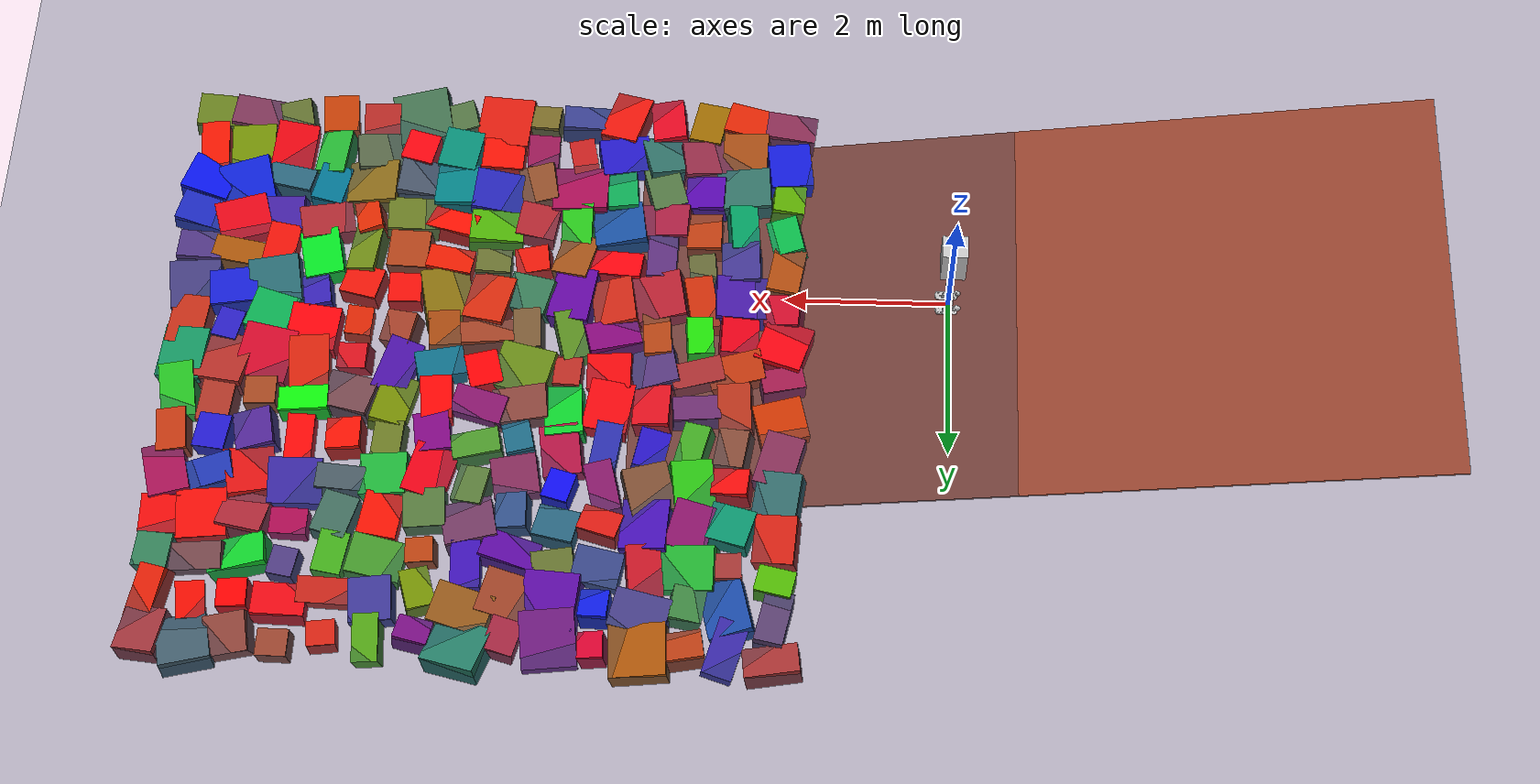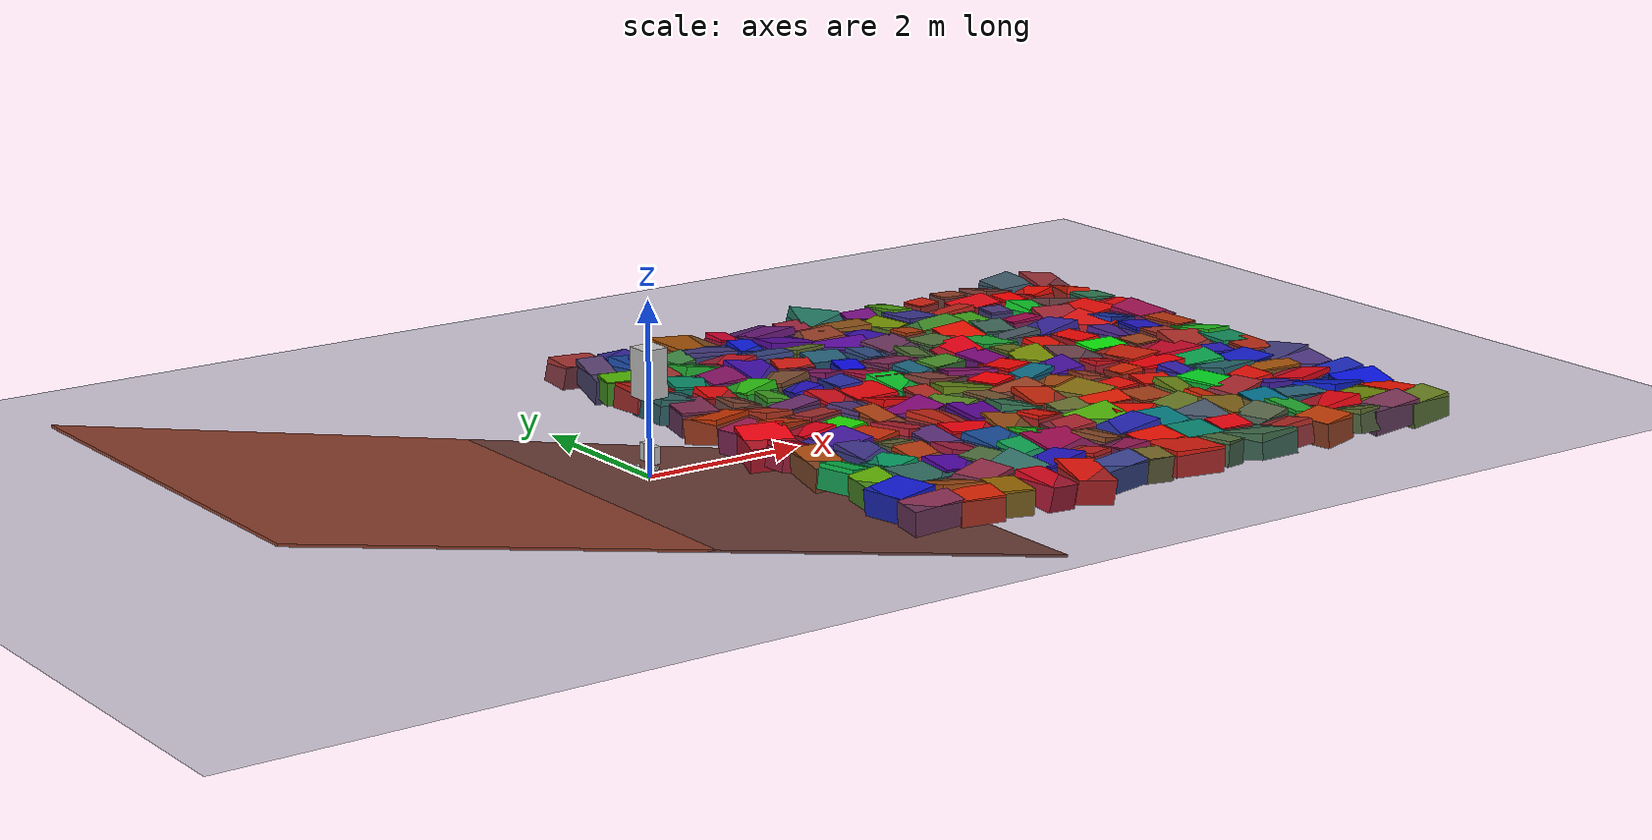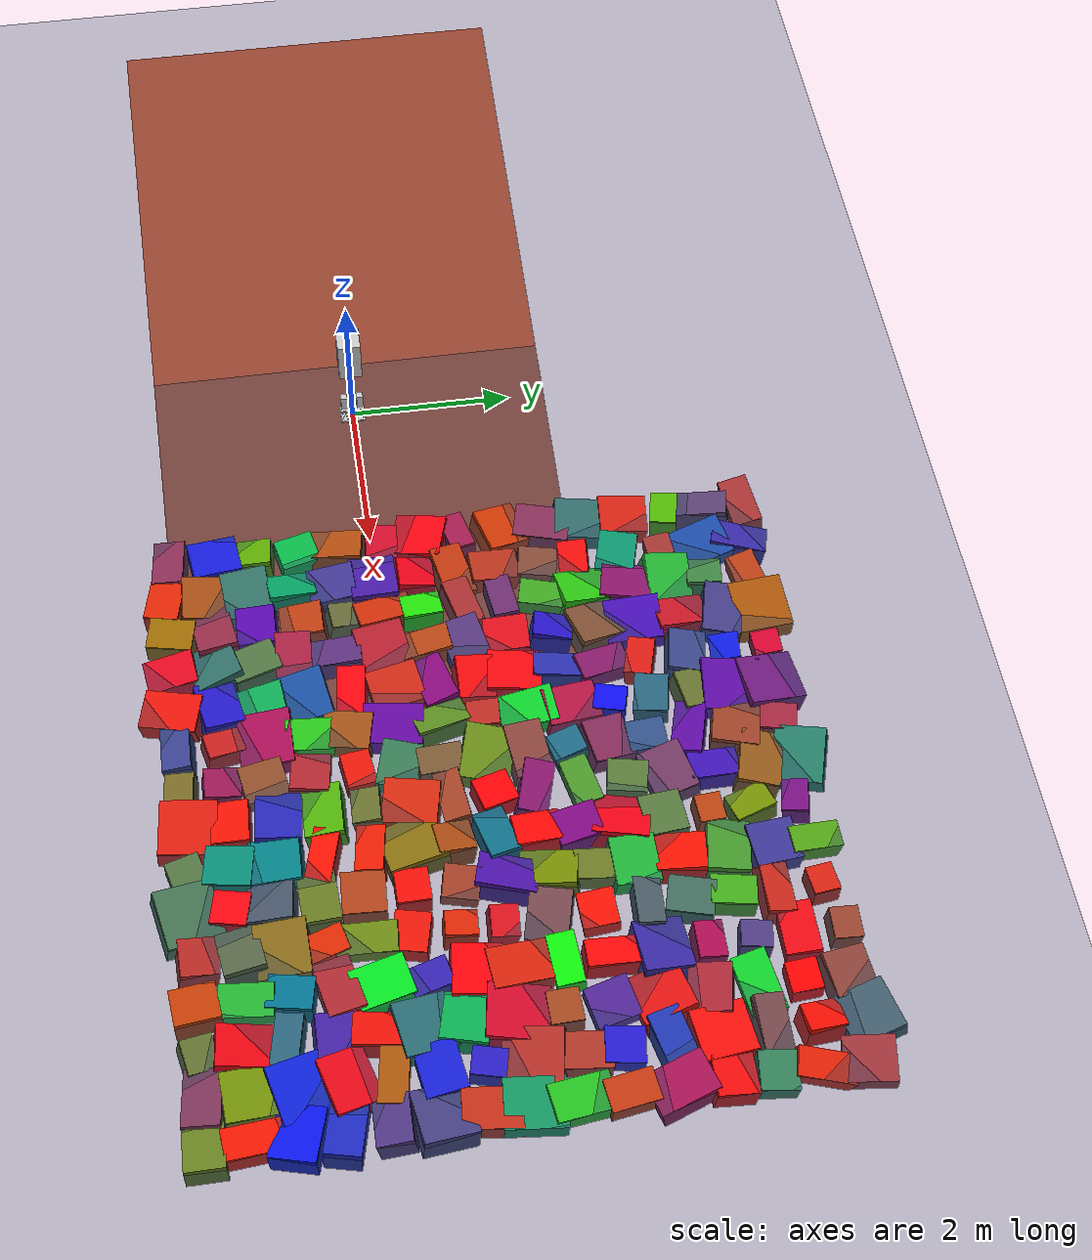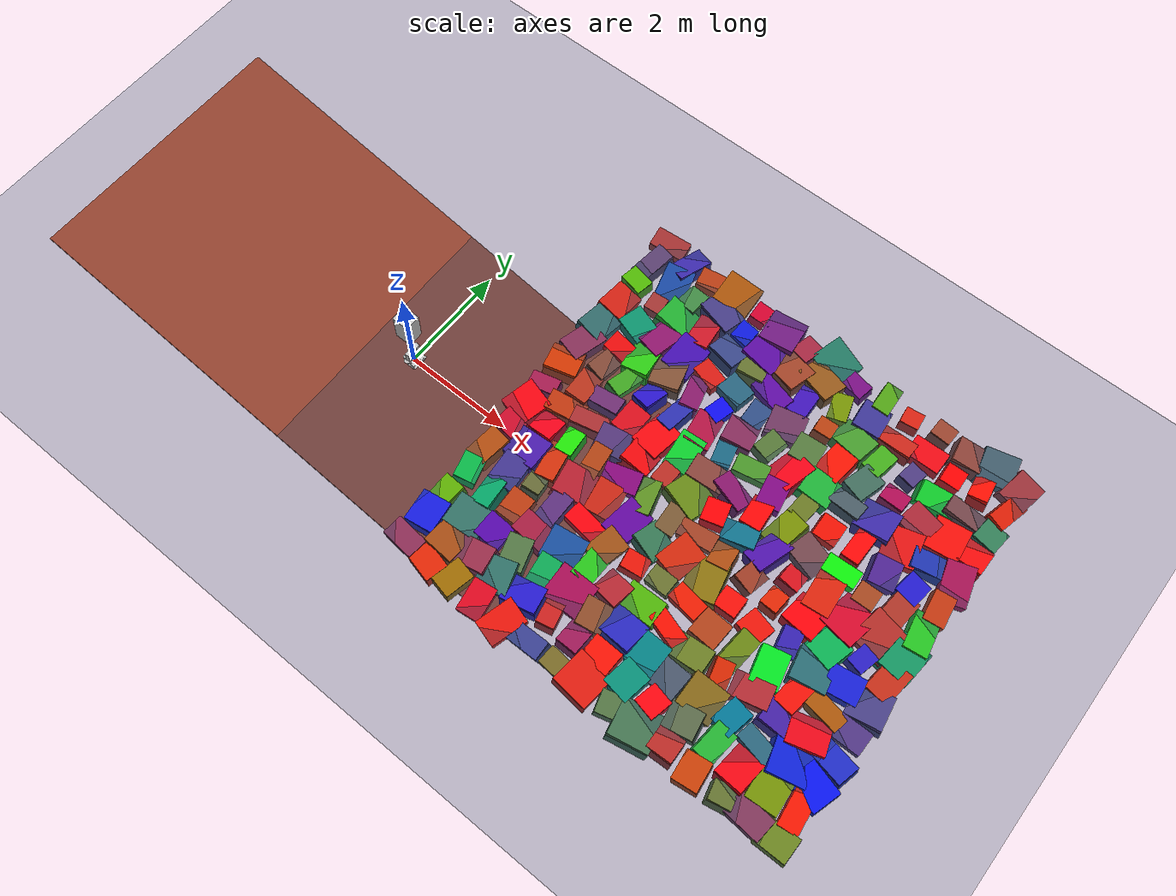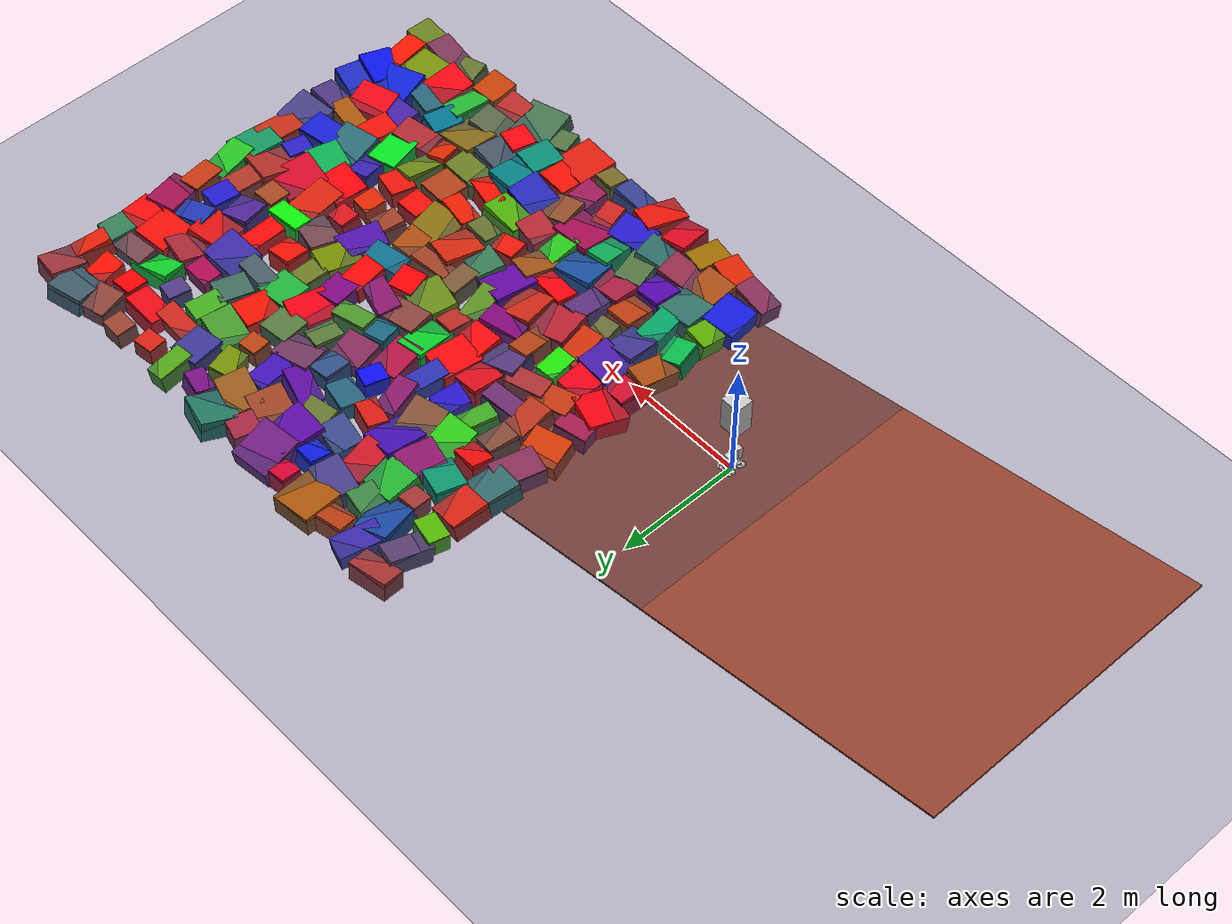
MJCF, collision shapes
<mujoco model="bhr8_fc2">
  <compiler angle="radian" meshdir="../meshes/" />

  <default>
      <joint limited="true" />
      <motor ctrllimited="true" />
      <geom condim="4" contype="1" conaffinity="15" solref="0.001 2" friction="0.9 0.2 0.2" />
      <equality solref="0.001 2" />
      <default class="visualgeom">
          <geom material="visualgeom" condim="1" contype="0" conaffinity="0" />
      </default>
      <default class="visualgeom2">
          <geom material="visualgeom2" condim="1" contype="0" conaffinity="0" />
      </default>
      <default class="obstacle">
          <geom material="obstacle" condim="3" contype="1" conaffinity="15" />
      </default>

  </default>

  <asset>
    <mesh name="torso" file="torso.stl" />
    <mesh name="rhip1" file="rhip1.stl" />
    <mesh name="rhip2" file="rhip2.stl" />
    <mesh name="rthigh" file="rthigh.stl" />
    <mesh name="rcalf" file="rcalf.stl" />
    <mesh name="rankle" file="rankle.stl" />
    <mesh name="rfoot" file="rfoot_small.stl" />
    <mesh name="lhip1" file="lhip1.stl" />
    <mesh name="lhip2" file="lhip2.stl" />
    <mesh name="lthigh" file="lthigh.stl" />
    <mesh name="lcalf" file="lcalf.stl" />
    <mesh name="lankle" file="lankle.stl" />
    <mesh name="lfoot" file="lfoot_small.stl" />
    <mesh name="rshoulder1" file="rshoulder1.stl" />
    <mesh name="rshoulder2" file="rshoulder2.stl" />
    <mesh name="rbigarm" file="rbigarm.stl" />
    <mesh name="rforearm" file="rforearm.stl" />
    <mesh name="lshoulder1" file="lshoulder1.stl" />
    <mesh name="lshoulder2" file="lshoulder2.stl" />
    <mesh name="lbigarm" file="lbigarm.stl" />
    <mesh name="lforearm" file="lforearm.stl" />
  </asset>

  <asset>
    <texture name="grid" type="2d" builtin="checker" width="512" height="512" rgb1=".1 .2 .3" rgb2=".2 .3 .4" />
    <material name="grid" texture="grid" texrepeat="1 1" texuniform="true" reflectance=".2" />
  </asset>

  <option timestep="0.001" integrator="RK4">
    <flag frictionloss="enable" />
  </option>

  <visual>
    <map stiffness="300" force="0.1" zfar="30" />
    <rgba haze="0.15 0.25 0.35 1" />
    <global offwidth="2560" offheight="1440" elevation="-30" azimuth="120" />
  </visual>

  <worldbody>
    <light name="main_light" diffuse="2 2 2" specular="0.5 0.5 0.5" pos="0 0 40" dir="0 0 -1" castshadow="true" />
    <light name="aux_light1" diffuse=".8 .8 .8" pos=" 10 0 1" dir="-1 0 0" castshadow="false" />
    <light name="aux_light2" diffuse=".8 .8 .8" pos="-10 0 1" dir=" 1 0 0" castshadow="false" />
    <light name="aux_light3" diffuse=".8 .8 .8" pos="0  10 1" dir="0 -1 0" castshadow="false" />
    <light name="aux_light4" diffuse=".8 .8 .8" pos="0 -10 1" dir="0  1 0" castshadow="false" />
    <geom name="floor" type="plane" size="0 0 0.05" material="grid" />

    <body name="torso" pos="0 0 0.95" euler="0 0 0">
      <inertial pos="-0.012982 0.001904 0.240391" mass="24.091719" fullinertia="0.717329 0.608806 0.242843 0.001910 -0.031575 0.004632" />
      <freejoint name="torso" />

      <geom type="mesh" contype="0" conaffinity="0" group="1" density="0" rgba="0.752941 0.752941 0.752941 1" mesh="torso" />
      <geom size="0.15 0.14 0.28" pos="0 0 0.25" type="box" rgba="0.752941 0.752941 0.752941 0" />
      <site name="imu" pos="0 0 0" size="0.02" rgba="1 0 0 1" type="sphere" />

      <body name="rhip1" pos="0 -0.1 0.02324">
        <inertial pos="-0.078509 0 -0.118031" quat="0.312936 0.634303 0.633788 0.313119" mass="2.58958" diaginertia="0.011987 0.0111943 0.00318774" />
        <joint name="rhipYaw" pos="0 0 0" axis="0 0 1" range="-0.78 0.78" actuatorfrcrange="-300 300" />
        <geom type="mesh" contype="0" conaffinity="0" group="1" density="0" rgba="0.752941 0.752941 0.752941 1" mesh="rhip1" />

        <body name="rhip2" pos="-0.054 0 -0.13924">
          <inertial pos="0.051206 -0.00273 -0.000288" quat="-0.0508471 0.718896 0.0506336 0.691404" mass="2.70709" diaginertia="0.0040419 0.00361648 0.00344663" />
          <joint name="rhipRoll" pos="0 0 0" axis="1 0 0" range="-0.78 0.78" actuatorfrcrange="-300 300" />
          <geom type="mesh" contype="0" conaffinity="0" group="1" density="0" rgba="0.752941 0.752941 0.752941 1" mesh="rhip2" />

          j
          <body name="rthigh" pos="0.055 -0.0001 0">
            <inertial pos="0.005701 -0.002335 -0.170006" quat="0.999478 -0.00792791 -0.00348956 0.0311153" mass="3.59646" diaginertia="0.0430693 0.0409464 0.00582637" />
            <joint name="rhipPitch" pos="0 0 0" axis="0 1 0" range="-1.4 0.7" actuatorfrcrange="-300 300" />
            <geom type="mesh" contype="0" conaffinity="0" group="1" density="0" rgba="0.752941 0.752941 0.752941 1" mesh="rthigh" />

            <body name="rcalf" pos="0 0 -0.375">
              <inertial pos="0.003761 0 -0.143175" quat="0.99988 -0.000702889 -0.0153326 0.00193635" mass="2.51427" diaginertia="0.0176306 0.017018 0.00210037" />
              <joint name="rknee" pos="0 0 0" axis="0 1 0" range="0 1.8" actuatorfrcrange="-300 300" />
              <geom size="0.04 0.04 0.1" pos="0 0 -0.18" type="box" rgba="0.752941 0.752941 0.752941 0" />
              <geom type="mesh" contype="0" conaffinity="0" group="1" density="0" rgba="0.752941 0.752941 0.752941 1" mesh="rcalf" />

              <body name="rankle" pos="0 0 -0.35">
                <inertial pos="-0.025377 0.000124 0.003585" quat="0.513827 0.48578 0.48578 0.513827" mass="0.139581" diaginertia="0.000117 0.000111225 3.97754e-05" />
                <joint name="rankle1" pos="0 0 0" axis="0 1 0" range="-1 0.6" actuatorfrcrange="-300 300" />
                <geom type="mesh" contype="0" conaffinity="0" group="1" density="0" rgba="0.752941 0.752941 0.752941 1" mesh="rankle" />

                <body name="rfoot" pos="0.031 0 0">
                  <inertial pos="-0.016884 0.000166 -0.054343" quat="-0.00139322 0.658253 -0.0050555 0.752779" mass="1.50445" diaginertia="0.00652476 0.00619614 0.0011981" />
                  <joint name="rankle2" pos="0 0 0" axis="1 0 0" range="-0.78 0.78" actuatorfrcrange="-300 300" />
                  <geom type="mesh" contype="0" conaffinity="0" group="1" density="0" rgba="0.752941 0.752941 0.752941 1" mesh="rfoot" />
                  <geom type="mesh" rgba="0.752941 0.752941 0.752941 0" mesh="rfoot" />
                </body>
              </body>
            </body>
          </body>
        </body>
      </body>

      <body name="lhip1" pos="0 0.1 0.02324">
        <inertial pos="-0.078509 0 -0.118031" quat="0.312936 0.634303 0.633788 0.313119" mass="2.58958" diaginertia="0.011987 0.0111943 0.00318774" />
        <joint name="lhipYaw" pos="0 0 0" axis="0 0 1" range="-0.78 0.78" actuatorfrcrange="-300 300" />
        <geom type="mesh" contype="0" conaffinity="0" group="1" density="0" rgba="0.752941 0.752941 0.752941 1" mesh="lhip1" />

        <body name="lhip2" pos="-0.054 0 -0.13924">
          <inertial pos="0.051206 0.002733 -0.00028" quat="0.0501181 0.718914 -0.051553 0.691371" mass="2.70722" diaginertia="0.00404191 0.00361648 0.00344661" />
          <joint name="lhipRoll" pos="0 0 0" axis="1 0 0" range="-0.78 0.78" actuatorfrcrange="-300 300" />
          <geom type="mesh" contype="0" conaffinity="0" group="1" density="0" rgba="0.752941 0.752941 0.752941 1" mesh="lhip2" />

          <body name="lthigh" pos="0.055 0 0">
            <inertial pos="0.004804 0.002343 -0.169952" quat="0.99957 0.00788906 -0.00488581 -0.0278185" mass="3.59646" diaginertia="0.0430607 0.0408405 0.00572671" />
            <joint name="lhipPitch" pos="0 0 0" axis="0 1 0" range="-1.4 0.7" actuatorfrcrange="-300 300" />
            <geom type="mesh" contype="0" conaffinity="0" group="1" density="0" rgba="0.752941 0.752941 0.752941 1" mesh="lthigh" />

            <body name="lcalf" pos="0 0 -0.375">
              <inertial pos="0.003757 -0.00029 -0.143175" quat="0.999882 0.000728441 -0.0153344 0.000562778" mass="2.51427" diaginertia="0.0176306 0.017019 0.00210036" />
              <joint name="lknee" pos="0 0 0" axis="0 1 0" range="0 1.8" actuatorfrcrange="-300 300" />
              <geom size="0.04 0.04 0.1" pos="0 0 -0.18" type="box" rgba="0.752941 0.752941 0.752941 0" />
              <geom type="mesh" contype="0" conaffinity="0" group="1" density="0" rgba="0.752941 0.752941 0.752941 1" mesh="lcalf" />

              <body name="lankle" pos="0 0 -0.35">
                <inertial pos="-0.025377 0.000124 0.003585" quat="0.513827 0.48578 0.48578 0.513827" mass="0.139581" diaginertia="0.000117 0.000111225 3.97754e-05" />
                <joint name="lankle1" pos="0 0 0" axis="0 1 0" range="-1 0.6" actuatorfrcrange="-300 300" />
                <geom type="mesh" contype="0" conaffinity="0" group="1" density="0" rgba="0.752941 0.752941 0.752941 1" mesh="lankle" />

                <body name="lfoot" pos="0.031 0 0">
                  <inertial pos="-0.016876 -0.000173 -0.054342" quat="0.0024359 0.658246 0.00581857 0.752776" mass="1.50435" diaginertia="0.00652477 0.00619511 0.00119811" />
                  <joint name="lankle2" pos="0 0 0" axis="1 0 0" range="-0.78 0.78" actuatorfrcrange="-300 300" />
                  <geom type="mesh" rgba="0.752941 0.752941 0.752941 0" mesh="lfoot" />
                  <geom type="mesh" contype="0" conaffinity="0" group="1" density="0" rgba="0.752941 0.752941 0.752941 1" mesh="lfoot" />
                </body>
              </body>
            </body>
          </body>
        </body>
      </body>

      <body name="rshoulder1" pos="-0.02625 -0.13476 0.389">
        <inertial pos="-0.072957 -0.077869 0" quat="0.0679918 0.703732 -0.0683079 0.703898" mass="1.93819" diaginertia="0.007542 0.00713155 0.00236245" />
        <joint name="rshoulderPitch" pos="0 0 0" axis="0 -1 0" range="-3.14 3.14" actuatorfrcrange="-300 300" />
        <geom type="mesh" contype="0" conaffinity="0" group="1" density="0" rgba="0.752941 0.752941 0.752941 1" mesh="rshoulder1" />

        <body name="rshoulder2" pos="-0.049 -0.08424 0">
          <inertial pos="0.051 0 -0.017501" quat="0.45725 0.539372 0.539372 0.45725" mass="2.11646" diaginertia="0.003457 0.00313511 0.00264589" />
          <joint name="rshoulderRoll" pos="0 0 0" axis="1 0 0" range="-1.57 0" actuatorfrcrange="-300 300" />
          <geom type="mesh" contype="0" conaffinity="0" group="1" density="0" rgba="0.752941 0.752941 0.752941 1" mesh="rshoulder2" />

          <body name="rbigarm" pos="0.049 0 -0.05">
            <inertial pos="0.002752 0 -0.123717" quat="0.999552 0 0.0299255 0" mass="2.50306" diaginertia="0.0121441 0.011971 0.00122592" />
            <joint name="rshoulderYaw" pos="0 0 0" axis="0 0 1" range="-1.57 1.57" actuatorfrcrange="-300 300" />
            <geom type="mesh" contype="0" conaffinity="0" group="1" density="0" rgba="0.752941 0.752941 0.752941 1" mesh="rbigarm" />

            <body name="rforearm" pos="0 -0.01 -0.30324" quat="0.696707 0 -0.717356 0">
              <inertial pos="0.002409 0.01 -0.09" quat="0.707065 -0.00771561 -0.00771561 0.707065" mass="0.381283" diaginertia="0.001374 0.00136863 3.9367e-05" />
              <joint name="relbow" pos="0 0 0" axis="0 -1 0" range="0 2" actuatorfrcrange="-300 300" />
              <geom type="mesh" contype="0" conaffinity="0" group="1" density="0" rgba="0.752941 0.752941 0.752941 1" mesh="rforearm" />
            </body>
          </body>
        </body>
      </body>

      <body name="lshoulder1" pos="-0.02625 0.13476 0.389">
        <inertial pos="-0.072957 0.077869 0" quat="-0.0683079 0.703898 0.0679918 0.703732" mass="1.93819" diaginertia="0.007542 0.00713155 0.00236245" />
        <joint name="lshoulderPitch" pos="0 0 0" axis="0 1 0" range="-3.14 3.14" actuatorfrcrange="-300 300" />
        <geom type="mesh" contype="0" conaffinity="0" group="1" density="0" rgba="0.752941 0.752941 0.752941 1" mesh="lshoulder1" />

        <body name="lshoulder2" pos="-0.049 0.08424 0">
          <inertial pos="0.051 0 -0.017501" quat="0.45725 0.539372 0.539372 0.45725" mass="2.11646" diaginertia="0.003457 0.00313511 0.00264589" />
          <joint name="lshoulderRoll" pos="0 0 0" axis="1 0 0" range="0 1.57" actuatorfrcrange="-300 300" />
          <geom type="mesh" contype="0" conaffinity="0" group="1" density="0" rgba="0.752941 0.752941 0.752941 1" mesh="lshoulder2" />

          <body name="lbigarm" pos="0.049 0 -0.05">
            <inertial pos="0.002752 0 -0.123717" quat="0.999552 0 0.0299255 0" mass="2.50306" diaginertia="0.0121441 0.011971 0.00122592" />
            <joint name="lshoulderYaw" pos="0 0 0" axis="0 0 1" range="-1.57 1.57" actuatorfrcrange="-300 300" />
            <geom type="mesh" contype="0" conaffinity="0" group="1" density="0" rgba="0.752941 0.752941 0.752941 1" mesh="lbigarm" />

            <body name="lforearm" pos="0 0.01 -0.30324" quat="0.696707 0 -0.717356 0">
              <inertial pos="0.0024 -0.01 -0.09" quat="0.707065 -0.00771561 -0.00771561 0.707065" mass="0.381283" diaginertia="0.001374 0.00136863 3.9367e-05" />
              <joint name="lelbow" pos="0 0 0" axis="0 1 0" range="0 2" actuatorfrcrange="-300 300" />
              <geom type="mesh" contype="0" conaffinity="0" group="1" density="0" rgba="0.752941 0.752941 0.752941 1" mesh="lforearm" />
            </body>
          </body>
        </body>
      </body>
    </body>
  <geom pos="1.999854532044694 -2.46126150641404 -0.145" type="box" size="0.3144736095679356 0.18792187735148166 0.14795310612708515" quat="0.9970281984431242 0.04032174894182146 -0.04543843477206326 -0.0473737977894519" rgba="0.5178014307029457 0.16718661640755172 0.31501195288950257 0.95" /><geom pos="1.999854532044694 -1.9127992831286744 -0.145" type="box" size="0.2659488408504377 0.29565623175472266 0.15300595093975508" quat="0.9965554234260146 -0.011923277358217622 -0.048828703099654355 0.06596121019843042" rgba="0.07404635896207112 0.0971884974385726 0.8287651435993563 0.95" /><geom pos="1.999854532044694 -1.4190295342160943 -0.145" type="box" size="0.1953771200380241 0.20771364484925772 0.1514605133739117" quat="0.9951581608524473 0.05475986023513221 -0.07348965091787532 -0.0355086440711554" rgba="0.3462936216260074 0.6496541443733868 0.004052234000605837 0.95" /><geom pos="1.999854532044694 -0.9063265158502327 -0.145" type="box" size="0.1939704383762666 0.23683365788155103 0.1502700581510344" quat="0.9884475431578554 -0.012823210620556158 0.08372737826347824 0.12568510581490797" rgba="0.030249762564137805 0.6979707450361804 0.2717794923996818 0.95" /><geom pos="1.999854532044694 -0.40548179267579876 -0.145" type="box" size="0.19869810356500234 0.31630057363976527 0.14736359589764603" quat="0.9948019964851956 0.05916898133526741 -0.03042514031749158 -0.07708651161828847" rgba="0.6637258870314162 0.28275214213231226 0.053521970836271526 0.95" /><geom pos="1.999854532044694 0.12779203448464038 -0.145" type="box" size="0.21732155823943589 0.19292091177388265 0.15481844455009253" quat="0.994227753230782 -0.030179097979752018 0.09248852873030441 -0.04523570275902917" rgba="0.7900310527402576 0.04599864001050564 0.16397030724923672 0.95" /><geom pos="1.999854532044694 0.6130516832860788 -0.145" type="box" size="0.2928010756974569 0.31474189686254617 0.15099355746496623" quat="0.985342081773878 0.0865166821529622 -0.025401650173899552 -0.14481229838382673" rgba="0.929653852733742 0.009490213658591122 0.06085593360766686 0.95" /><geom pos="1.999854532044694 1.0715298189132048 -0.145" type="box" size="0.2602826790333971 0.15014050459623224 0.1475120952803263" quat="0.9930819975704858 0.007392707748075766 -0.02984437889203594 0.11332610918104274" rgba="0.6111930524821826 0.09540687338610783 0.2934000741317096 0.95" /><geom pos="1.999854532044694 1.6053401637633549 -0.145" type="box" size="0.29577918306245016 0.25624467946901963 0.14906335265157472" quat="0.9877887362401087 -0.07857751979023544 -0.00558683753375791 0.1344164171042937" rgba="0.7881049132658876 0.20502904683129416 0.006866039902818227 0.95" /><geom pos="1.999854532044694 2.1299232577560154 -0.145" type="box" size="0.234555690961252 0.337682316260309 0.14792019159715075" quat="0.9913427959127545 -0.0042522060277817 0.008919133962920094 -0.13092680697676629" rgba="0.5008141165126317 0.17475358565810498 0.3244322978292633 0.95" /><geom pos="1.999854532044694 2.638774121087687 -0.145" type="box" size="0.26692934266229396 0.34861675697111766 0.15233249571957694" quat="0.9944535003081559 -0.02997471164063262 0.07410548403388961 -0.06835297815765083" rgba="0.19169881528746058 0.4050205746535969 0.4032806100589425 0.95" /><geom pos="1.999854532044694 3.134017307145733 -0.145" type="box" size="0.249178517549716 0.2938309992890631 0.1534880674065783" quat="0.9957583942557323 -0.0390945006410889 0.07464859679449282 -0.03693815487382705" rgba="0.8065735988100581 0.12192659607673241 0.07149980511320951 0.95" /><geom pos="1.999854532044694 3.670757768366496 -0.145" type="box" size="0.22235082937563025 0.16422255501020444 0.15129116064114703" quat="0.9938700911071422 0.03388612133293848 -0.003667971827133178 -0.10516900097636105" rgba="0.30227274775716717 0.6878152848387213 0.009911967404111488 0.95" /><geom pos="1.999854532044694 4.1290571053184255 -0.145" type="box" size="0.17085901806966486 0.34133689147487334 0.15494993124640236" quat="0.9909273668495763 0.09056165664909716 -0.015835039028520362 -0.09803464445032423" rgba="0.33719010611506794 0.24014789966357852 0.42266199422135353 0.95" /><geom pos="1.999854532044694 4.647202675917644 -0.145" type="box" size="0.32493540123877823 0.1809874060865031 0.14954163583093855" quat="0.9935782577643939 0.07866596809515991 0.05210467658612781 0.06244208388080919" rgba="0.6280114365734158 0.18687972915400575 0.1851088342725784 0.95" /><geom pos="2.547917299096909 -2.5448061328977802 -0.145" type="box" size="0.2628903965637234 0.20706254192642343 0.15351800848579067" quat="0.9926156972835583 0.015874781800701673 -0.014676274602790803 -0.11935943939563026" rgba="0.8464941755869337 0.1378383718666339 0.01566745254643237 0.95" /><geom pos="2.547917299096909 -2.0417606133636976 -0.145" type="box" size="0.28122475538616587 0.31735419523226766 0.1465889925852296" quat="0.9950663687013143 -0.0844083958340025 0.04931055180625909 -0.016929680235391105" rgba="0.6330305676416411 0.29106921889312243 0.07590021346523645 0.95" /><geom pos="2.547917299096909 -1.5540621990921655 -0.145" type="box" size="0.32713543448912463 0.28051828153340175 0.14773266130327664" quat="0.9982064265239209 0.030214517672543312 0.03075308532537183 0.04153625778918968" rgba="0.1907012150455939 0.4265585261572821 0.382740258797124 0.95" /><geom pos="2.547917299096909 -1.0342251831727896 -0.145" type="box" size="0.17245988854614924 0.28423227334386353 0.15413625966711159" quat="0.9938599718704091 -0.0557966864025301 -0.07723022918150055 0.056254580265257585" rgba="0.010802014961767026 0.6111769930375532 0.37802099200067973 0.95" /><geom pos="2.547917299096909 -0.5139874017727633 -0.145" type="box" size="0.23779843570282572 0.28209277295855945 0.14679058576781" quat="0.9965195771604429 0.0680051753635007 0.03935355416679288 0.02784468053673617" rgba="0.24844260280967645 0.20115609131241047 0.5504013058779131 0.95" /><geom pos="2.547917299096909 -0.02239896633696059 -0.145" type="box" size="0.3110195411709831 0.2809181168035675 0.15412080534228528" quat="0.9972116978791968 0.006688315551517015 -0.07401849772607894 0.006734837959998062" rgba="0.2697410459702375 0.09580826399251112 0.6344506900372514 0.95" /><geom pos="2.547917299096909 0.4742658965037627 -0.145" type="box" size="0.22659991342477165 0.21724775989858697 0.1527681602605882" quat="0.9938908491127292 -0.07881771692614861 -0.07640085881889619 -0.011474158804134731" rgba="0.9064131860156545 0.0018843720750834762 0.09170244190926206 0.95" /><geom pos="2.547917299096909 0.9369618204464492 -0.145" type="box" size="0.33699601628027914 0.19361867601749067 0.1517705288726579" quat="0.9902218365320229 -0.05700931722058981 0.06432562559181164 0.10987659485719324" rgba="0.7333368351851164 0.2098657285505944 0.05679743626428921 0.95" /><geom pos="2.547917299096909 1.435453598498242 -0.145" type="box" size="0.19965106378149414 0.29591367352652953 0.15435006134244028" quat="0.9958919428751982 -0.0738788259171528 0.04188868227100299 0.03140852583240694" rgba="0.7005255082108964 0.19431711936927382 0.10515737241982975 0.95" /><geom pos="2.547917299096909 1.9789161108009754 -0.145" type="box" size="0.1852115373799683 0.23429991020786553 0.1460599181404333" quat="0.9912508999299042 -0.036732782243859695 0.09664049677850828 -0.08205467981281456" rgba="0.5077104421300194 0.2825614122699461 0.20972814560003455 0.95" /><geom pos="2.547917299096909 2.449508942351299 -0.145" type="box" size="0.21927939890853723 0.17599460542171802 0.15006190008863232" quat="0.9922978846363117 0.08708756457527542 0.07808811475799496 -0.0407788005732195" rgba="0.9145468909989736 0.044158308698095644 0.041294800302930784 0.95" /><geom pos="2.547917299096909 2.9746806086624797 -0.145" type="box" size="0.27011928616239417 0.23353392310092908 0.1463314726737556" quat="0.9883919600064857 0.01907816375542387 0.048099129075124224 -0.14284197857938485" rgba="0.03671303333633391 0.5552714266529686 0.4080155400106975 0.95" /><geom pos="2.547917299096909 3.511254541361006 -0.145" type="box" size="0.15525370302074776 0.16256806313836475 0.1544162258281519" quat="0.9976071531526319 0.058923765738539476 -0.0009632105341162455 0.036152870361254544" rgba="0.6105337327460038 0.19905967632490554 0.1904065909290907 0.95" /><geom pos="2.547917299096909 4.013193643107545 -0.145" type="box" size="0.2617216521807334 0.34947854011206697 0.14651893652704104" quat="0.9861674161812813 0.05792843732913404 0.08427785322777236 0.13044296403508343" rgba="0.09416090275540301 0.2765405768642569 0.6292985203803401 0.95" /><geom pos="2.547917299096909 4.487709777566456 -0.145" type="box" size="0.18289116046484175 0.3402978482177698 0.14783210770956917" quat="0.9862731505659487 -0.06350839395266189 -0.048818017855572535 -0.1443909883023315" rgba="0.21517304676070637 0.14795665250503415 0.6368703007342595 0.95" /><geom pos="3.0220738872554835 -2.4969894857874104 -0.145" type="box" size="0.2029309442048338 0.27165464202000494 0.15176538878624346" quat="0.9943958857136453 0.0037121703279554257 0.019104760197198555 -0.10391366803764703" rgba="0.5913223087349118 0.4026203850188919 0.006057306246196326 0.95" /><geom pos="3.0220738872554835 -1.9924385864971705 -0.145" type="box" size="0.3326405371385413 0.23704896202024434 0.1462616084218226" quat="0.9926967754840126 0.017958496353744212 -0.0887292086036288 0.07973538670458927" rgba="0.5629775377137892 0.16443889385561436 0.2725835684305964 0.95" /><geom pos="3.0220738872554835 -1.4724488022870421 -0.145" type="box" size="0.2424976517070791 0.23287515752932772 0.154294870232598" quat="0.9969661642126947 0.049127032771215544 0.05952887926175959 -0.010065515384768797" rgba="0.32527094980924864 0.02354055797694098 0.6511884922138104 0.95" /><geom pos="3.0220738872554835 -0.924332220302579 -0.145" type="box" size="0.21369161203463727 0.25663499311648996 0.145880342958228" quat="0.9973613352586034 0.07145142039885152 0.010648991817094498 0.007187518865504938" rgba="0.7119723683539029 0.2270416794447559 0.06098595220134123 0.95" /><geom pos="3.0220738872554835 -0.45612431209398085 -0.145" type="box" size="0.16393294084773885 0.16523218781888635 0.14593672017827491" quat="0.994518542867473 -0.0871177515167379 0.020083963687176024 0.054221763767316696" rgba="0.38872804205401823 0.40225793791923675 0.20901402002674502 0.95" /><geom pos="3.0220738872554835 0.045506956166505574 -0.145" type="box" size="0.17307532755685415 0.34001524755612544 0.14713460136414033" quat="0.9936953288809562 -0.03144345328548353 -0.044282403868198976 0.09808145244288374" rgba="0.7849971637451515 0.17740562257415132 0.037597213680697184 0.95" /><geom pos="3.0220738872554835 0.49833327385741555 -0.145" type="box" size="0.15879467234487704 0.23954561308661607 0.14634799434844267" quat="0.9975347240777155 -0.027372107716105643 -0.04491276528731274 0.046455198768499205" rgba="0.12257925971658035 0.8545488103941483 0.022871929889271336 0.95" /><geom pos="3.0220738872554835 0.9993077536979587 -0.145" type="box" size="0.3175285341679923 0.15926842415823572 0.15415927485491257" quat="0.9912335567179021 -0.04259341111553491 0.02108458358819572 0.12327723918401522" rgba="0.6382208547704976 0.17711969013061826 0.18465945509888412 0.95" /><geom pos="3.0220738872554835 1.4827731298040314 -0.145" type="box" size="0.2842299389232468 0.15344540623533054 0.1549516912454658" quat="0.9978041109630731 0.007448810291512007 -0.03909570177860876 0.052943342101442595" rgba="0.40888356535374204 0.16956967258471325 0.42154676206154473 0.95" /><geom pos="3.0220738872554835 1.9610746061372506 -0.145" type="box" size="0.1605788839172445 0.2689351279600405 0.14893365278866688" quat="0.9890455388850838 -0.02030637197697812 0.07097581237930806 -0.127824126540118" rgba="0.24039173442152095 0.6324165312130153 0.12719173436546372 0.95" /><geom pos="3.0220738872554835 2.4611955463328403 -0.145" type="box" size="0.2463671853954288 0.3062409894024243 0.1469220262978204" quat="0.9902221962105809 -0.08560925533658786 -0.08179216445757972 0.07376380796808694" rgba="0.16584252002896893 0.763044037504849 0.07111344246618212 0.95" /><geom pos="3.0220738872554835 3.0036443990702493 -0.145" type="box" size="0.2470011243244407 0.3026566374904338 0.15011780009571302" quat="0.9916499036973452 -0.003995291907173932 -0.05531308517839422 -0.11642580791074739" rgba="0.5266988621789024 0.07312019342035851 0.4001809444007391 0.95" /><geom pos="3.0220738872554835 3.507911437196178 -0.145" type="box" size="0.3398083391801689 0.2685392718515348 0.15255822822464574" quat="0.992854608960385 -0.07608849281038205 0.09120231658997827 -0.011506701377308179" rgba="0.13119768970950263 0.68059098355905 0.18821132673144736 0.95" /><geom pos="3.0220738872554835 3.9756154224580387 -0.145" type="box" size="0.19388036780366363 0.20979426266107434 0.14929781549164944" quat="0.9926636701503266 0.027731206178920484 -0.09546592593576393 -0.06881914815495102" rgba="0.23682612404786307 0.5124409784916041 0.25073289746053284 0.95" /><geom pos="3.0220738872554835 4.498121609797169 -0.145" type="box" size="0.22824329974261698 0.1757652612748924 0.14798624259554566" quat="0.9925381606370911 0.08365134567588468 0.019055844562594827 0.08664483154671972" rgba="0.7015008623255813 0.22685532932932065 0.07164380834509806 0.95" /><geom pos="3.537318477421527 -2.5177028117199907 -0.145" type="box" size="0.20860555910524353 0.2962987567413714 0.14745550973313723" quat="0.9938301714240487 0.06801336826983925 0.054740191988819326 0.06840528842760853" rgba="0.8522110132443452 0.027572849333019317 0.12021613742263546 0.95" /><geom pos="3.537318477421527 -2.0002978537753044 -0.145" type="box" size="0.28921922612265966 0.2890201206560604 0.15243042952920613" quat="0.9821111763113931 0.10226833631416539 -0.08035846354383347 0.13616659681676377" rgba="0.1818392179091144 0.42598886967850574 0.39217191241237986 0.95" /><geom pos="3.537318477421527 -1.5475126530143195 -0.145" type="box" size="0.2141784145245781 0.2917884547255894 0.15395669577177" quat="0.9894823348373343 0.013990851870383188 -0.011390320946970662 0.14352430350823334" rgba="0.30630371170894555 0.4433515501231541 0.25034473816790037 0.95" /><geom pos="3.537318477421527 -1.0809360995606376 -0.145" type="box" size="0.3400649078350089 0.21181678606931398 0.14571336888220396" quat="0.99524512892571 -0.0060901168982464915 0.0942981783969033 -0.023619851329730972" rgba="0.6398984243779127 0.11256296089559245 0.24753861472649488 0.95" /><geom pos="3.537318477421527 -0.5561180302618047 -0.145" type="box" size="0.18059391495790034 0.2965142842647729 0.1499452792841603" quat="0.9981040322085907 0.05775267508325267 -0.02019841347864376 -0.006707719629393804" rgba="0.3503839595233945 0.17920569881334472 0.4704103416632608 0.95" /><geom pos="3.537318477421527 -0.02393983731872229 -0.145" type="box" size="0.3190255843485796 0.29685679409494103 0.1484211900677528" quat="0.9914261203473055 -0.03514146094607162 0.08525784651757613 0.09257659111703849" rgba="0.696419812572088 0.1209488164664226 0.18263137096148946 0.95" /><geom pos="3.537318477421527 0.4847421776116825 -0.145" type="box" size="0.16734527718578818 0.3258524555383582 0.1484201836243061" quat="0.9950968005979905 0.083215427773084 0.012179816207711271 0.05204999613191093" rgba="0.6763943684790383 0.2517920078431132 0.07181362367784849 0.95" /><geom pos="3.537318477421527 0.9518433205739343 -0.145" type="box" size="0.2785263657716036 0.24510388349928086 0.14553856550493233" quat="0.9899608899675894 0.01703016683760153 0.08041972278482723 0.11497859774442099" rgba="0.3240576106352753 0.20660679158015058 0.4693355977845741 0.95" /><geom pos="3.537318477421527 1.4708404609135917 -0.145" type="box" size="0.2201525478854277 0.26656744423009243 0.15216461654806387" quat="0.9968799382791502 0.04811912590433248 0.061465161827331555 -0.011703514869493881" rgba="0.8393959707087462 0.054618924167143736 0.10598510512411011 0.95" /><geom pos="3.537318477421527 2.006419262258712 -0.145" type="box" size="0.18382907656403566 0.2361020008805502 0.1480694554393698" quat="0.9883230290538815 -0.08074819495739892 -0.08152772267526295 -0.10025242983722679" rgba="0.15608141250446195 0.07576810010870548 0.7681504873868326 0.95" /><geom pos="3.537318477421527 2.5247667241187326 -0.145" type="box" size="0.27165143893814747 0.2924876782898004 0.14786501229308208" quat="0.9851865827932264 -0.08217158913156808 -0.053215587032295314 0.14079534197055726" rgba="0.49176480123133504 0.3073630440230836 0.20087215474558134 0.95" /><geom pos="3.537318477421527 3.0124958041341854 -0.145" type="box" size="0.28040433168085244 0.3317065385927594 0.1514054885965403" quat="0.9952016877834943 0.06799683149178933 0.06790619454670234 -0.018405984954546047" rgba="0.2612961477419389 0.0547802583754661 0.683923593882595 0.95" /><geom pos="3.537318477421527 3.557055315866706 -0.145" type="box" size="0.20484609650675986 0.31720714054954186 0.14838231171017066" quat="0.992975906762231 -0.080378254206898 -0.0600921224178782 0.06266675086272945" rgba="0.7719311250858284 0.08305605549242066 0.14501281942175093 0.95" /><geom pos="3.537318477421527 4.076082480217076 -0.145" type="box" size="0.3379785218849032 0.2317444722525918 0.15482723114543454" quat="0.9910246640427531 -0.048524930221885115 0.027064232321742276 -0.12158525294929524" rgba="0.262463044279334 0.2298033203256255 0.5077336353950406 0.95" /><geom pos="3.537318477421527 4.550746762678093 -0.145" type="box" size="0.3353764351872882 0.32118364803004046 0.1480664550379005" quat="0.9979755888503596 0.01468765255836857 0.05409801927277747 0.030039993872582355" rgba="0.6469891841508842 0.3200695120743089 0.03294130377480686 0.95" /><geom pos="4.075691290056388 -2.544930443516855 -0.145" type="box" size="0.23523281688328196 0.3408448497182382 0.14864843679388282" quat="0.9876943473123387 0.055554200671347 0.0427545336249149 -0.13980578289018278" rgba="0.88546248158163 0.07693162368003485 0.03760589473833516 0.95" /><geom pos="4.075691290056388 -2.0099850763089577 -0.145" type="box" size="0.31342985056487704 0.23515099768927342 0.15170259276937198" quat="0.9927840116680609 -0.051695581714946946 -0.048453463610229036 0.09674572275608541" rgba="0.14053390408582278 0.09043536784498467 0.7690307280691926 0.95" /><geom pos="4.075691290056388 -1.497468626642997 -0.145" type="box" size="0.18905442680506315 0.28382783899375097 0.1451692899456774" quat="0.9941097721016542 0.08979982029994205 0.019084648723538905 0.05759799882977114" rgba="0.04561464401445714 0.6378284145256089 0.31655694145993396 0.95" /><geom pos="4.075691290056388 -0.9922957580909046 -0.145" type="box" size="0.31666937457531086 0.28292950715320375 0.14683860142866606" quat="0.9927247832549023 0.06970908749521047 0.05195198291798173 0.08330149640301698" rgba="0.09264215807759402 0.3012398042241996 0.6061180376982064 0.95" /><geom pos="4.075691290056388 -0.4433517841793062 -0.145" type="box" size="0.31427281133811735 0.16587058026930143 0.14769292377407747" quat="0.9967375514103455 0.03880405059669599 0.04160096299226949 -0.05725259071792383" rgba="0.9452212491660691 0.008490089836685106 0.04628866099724581 0.95" /><geom pos="4.075691290056388 0.07189017239764528 -0.145" type="box" size="0.258120552065347 0.30600407535398166 0.14682437357097827" quat="0.9924230093912703 0.019155153979962897 0.08239295181231997 0.08911258047229587" rgba="0.7745978850832581 0.14806445140426253 0.07733766351247937 0.95" /><geom pos="4.075691290056388 0.5382473105870176 -0.145" type="box" size="0.32156544431721 0.20032983018338754 0.151064978761816" quat="0.9871879640537602 0.08035676483934909 -0.03510683310136795 0.13330500456298727" rgba="0.5080281701399413 0.02655072508730279 0.46542110477275594 0.95" /><geom pos="4.075691290056388 0.9990147433360748 -0.145" type="box" size="0.2704840071103514 0.22092180209687387 0.1485416565701237" quat="0.9949943159955431 -0.07501499735552485 0.06599057382935164 -0.0020749636105278713" rgba="0.9240669326271431 0.03141882681076406 0.04451424056209282 0.95" /><geom pos="4.075691290056388 1.4788732447606012 -0.145" type="box" size="0.26900155464702946 0.3225421714573764 0.1458231703645422" quat="0.9968798835225254 -0.015549299570788547 -0.02771152495696639 -0.07225502401586663" rgba="0.9214002290098886 0.027969144917204616 0.050630626072906776 0.95" /><geom pos="4.075691290056388 1.9847237337009629 -0.145" type="box" size="0.15734130567917998 0.28588053376183337 0.15228586072163716" quat="0.9961382844746008 -0.03622316142809385 -0.03872869558597651 -0.06997491635123601" rgba="0.16337392524641947 0.17774638714330285 0.6588796876102777 0.95" /><geom pos="4.075691290056388 2.5102621312517073 -0.145" type="box" size="0.16885975228028122 0.3091407769604061 0.14892662793726696" quat="0.9892900196589929 -0.06865899719254648 0.03473472581061039 0.12403506734179996" rgba="0.5107838353158713 0.0923665896279235 0.39684957505620516 0.95" /><geom pos="4.075691290056388 2.9904255798867485 -0.145" type="box" size="0.24085257440393226 0.16174471382297245 0.14605189272538327" quat="0.9871934668426509 0.06090447106793134 0.012325102473872064 -0.1469278607893418" rgba="0.8265652139365685 0.10156232276511305 0.07187246329831849 0.95" /><geom pos="4.075691290056388 3.526223770176432 -0.145" type="box" size="0.2803276088543824 0.21567472654249792 0.15321134971998832" quat="0.9923862654289389 -0.07077995488154754 -0.01661432362759551 -0.09941661040976427" rgba="0.21586450613636066 0.2668095182526337 0.5173259756110056 0.95" /><geom pos="4.075691290056388 4.018634195898545 -0.145" type="box" size="0.16941525834441104 0.177024863668103 0.14994224432114137" quat="0.9942834379509602 0.09335379822177164 0.04208236150002923 -0.030242159720637415" rgba="0.04710224921750117 0.09954021328797188 0.8533575374945269 0.95" /><geom pos="4.075691290056388 4.514520563348886 -0.145" type="box" size="0.15010450143938564 0.1637753097300682 0.15319838181153234" quat="0.9964135189056748 0.04782364655140935 0.06643054347766045 0.021447169179152018" rgba="0.8156959283692479 0.006735283039587088 0.17756878859116504 0.95" /><geom pos="4.593121113341814 -2.512814076179742 -0.145" type="box" size="0.3004407184980827 0.16944995017631637 0.1528482250414859" quat="0.9961129448873818 0.07250885336751192 -0.049784160492587 0.004796308493490715" rgba="0.2148977384115397 0.2418139552328271 0.5432883063556332 0.95" /><geom pos="4.593121113341814 -1.9866881253979107 -0.145" type="box" size="0.15826354821719718 0.22478142089434894 0.14543192752884165" quat="0.9912347897790774 -0.07042956351694152 -0.004680882996999383 0.11167523202935221" rgba="0.762037059320068 0.12186285435308743 0.11610008632684453 0.95" /><geom pos="4.593121113341814 -1.4800716435915953 -0.145" type="box" size="0.3433276156322038 0.3124300961042348 0.15233262229519481" quat="0.9969233510287814 0.0728179631508621 0.028587002432272846 0.004915252591879011" rgba="0.6373938489243222 0.044225557978260686 0.3183805930974172 0.95" /><geom pos="4.593121113341814 -1.0028668050158283 -0.145" type="box" size="0.19298742014344053 0.2792605026505124 0.1509909698996118" quat="0.995091549715145 -0.06345696197666746 0.07580957708425023 -0.0043508257273753405" rgba="0.14986281054160977 0.7533831199644765 0.09675406949391374 0.95" /><geom pos="4.593121113341814 -0.5424835115166982 -0.145" type="box" size="0.22566817432841213 0.28728060082952056 0.1453867263872612" quat="0.9898430198372422 0.055952183414726346 0.05996820844262976 -0.11612046859531262" rgba="0.6076064755616026 0.3070981414415437 0.08529538299685369 0.95" /><geom pos="4.593121113341814 -0.017289063140364824 -0.145" type="box" size="0.2548251895222881 0.3496830797937592 0.15453279224213556" quat="0.9963394103699823 0.011339869247294798 0.04633057277858343 -0.0709412766663984" rgba="0.3699565128371478 0.023660473354880033 0.6063830138079721 0.95" /><geom pos="4.593121113341814 0.527742824447694 -0.145" type="box" size="0.1595013922815097 0.32097487858294604 0.1465748995688952" quat="0.9888187716058799 -0.029339111354636724 -0.06073231121624522 0.13299714222152334" rgba="0.34183825739358253 0.5354545346242947 0.12270720798212276 0.95" /><geom pos="4.593121113341814 1.0445881151239558 -0.145" type="box" size="0.16378353033119764 0.19299557118123917 0.14679764465897308" quat="0.998346611439275 0.051539419875489496 0.002326095122201882 -0.025344050743671326" rgba="0.7028130269516583 0.16559086572367107 0.13159610732467067 0.95" /><geom pos="4.593121113341814 1.5630139823922846 -0.145" type="box" size="0.22775378805511842 0.33637283712828836 0.1460811781378788" quat="0.9956246711009956 0.06482782660310817 0.04677063862818761 0.048387752120378734" rgba="0.04404194357116553 0.7905594214107029 0.16539863501813157 0.95" /><geom pos="4.593121113341814 2.0617088332801687 -0.145" type="box" size="0.235435832971274 0.31790564801117027 0.14658386802849852" quat="0.9954873162969902 -0.04494165051773617 0.04538620823551728 0.07018078969746805" rgba="0.6772489829650492 0.0706953190765715 0.2520556979583793 0.95" /><geom pos="4.593121113341814 2.537107977383153 -0.145" type="box" size="0.16186104375524768 0.18958768028354567 0.14503334171514337" quat="0.9900277069594416 0.029446131749286265 0.009025860740280419 -0.137464899576331" rgba="0.055280839840577634 0.044547065396663664 0.9001720947627587 0.95" /><geom pos="4.593121113341814 3.02828314482836 -0.145" type="box" size="0.2475333768602534 0.2002209530144033 0.1466269140090705" quat="0.9928901713205673 0.05028597078908448 0.003622318179341869 -0.10782999419373836" rgba="0.15156806186423255 0.3746783957390746 0.4737535423966929 0.95" /><geom pos="4.593121113341814 3.503590520863435 -0.145" type="box" size="0.2427339343358324 0.1698648935774892 0.1504930741099771" quat="0.9942739722960798 -0.07128891969540947 0.009745570451031353 0.07900747939163613" rgba="0.38419232324860697 0.43651426255962356 0.17929341419176947 0.95" /><geom pos="4.593121113341814 3.9643612768561614 -0.145" type="box" size="0.32619071805407124 0.3461141227805843 0.1543888378692879" quat="0.9962838272085637 -0.041019292165537555 0.05545106156696275 -0.051586171441501204" rgba="0.34411555395632865 0.03849450548608273 0.6173899405575887 0.95" /><geom pos="4.593121113341814 4.418470042326103 -0.145" type="box" size="0.3202687059522612 0.3432719397307487 0.1548903322403756" quat="0.9940496567027723 -0.08836060710562306 -0.022833286574339657 0.059467000472868375" rgba="0.42048547293860206 0.09856834799189343 0.48094617906950454 0.95" /><geom pos="5.117716694623532 -2.5088628936531148 -0.145" type="box" size="0.1924146323192081 0.16861537417249062 0.15306016038016593" quat="0.9974524748606154 0.05404126041629874 0.02110279296081785 -0.041506321160804355" rgba="0.4550657374329623 0.39796583358552207 0.14696842898151563 0.95" /><geom pos="5.117716694623532 -2.0479410732398544 -0.145" type="box" size="0.19375870128014108 0.21301881573278428 0.14665094576569784" quat="0.9965129657096438 -0.07392970599343024 -0.0381911497265689 -0.006143600480011266" rgba="0.5859347015610724 0.08797170106088277 0.32609359737804483 0.95" /><geom pos="5.117716694623532 -1.5679944486468849 -0.145" type="box" size="0.22601273918157078 0.2530508600765955 0.14588045125549007" quat="0.9915068042870485 -0.016031391050823338 0.0842174118091078 0.09779917740776303" rgba="0.548549993445421 0.2932047240935628 0.1582452824610162 0.95" /><geom pos="5.117716694623532 -1.0339391779236524 -0.145" type="box" size="0.2428117288959322 0.2265714781700773 0.14848689219559422" quat="0.9953653348652679 -0.020950152398910574 -0.05712990124983664 -0.07446553327680842" rgba="0.6744506256878414 0.14247561537666925 0.18307375893548933 0.95" /><geom pos="5.117716694623532 -0.4866245016022681 -0.145" type="box" size="0.20858374893593903 0.17008967558661242 0.1456100376324582" quat="0.9949380299575897 -0.020175266479345998 0.060518655277144444 0.07764513848299637" rgba="0.8867474801991337 0.08229242153260394 0.03096009826826232 0.95" /><geom pos="5.117716694623532 -0.017332629743645356 -0.145" type="box" size="0.2768958696162801 0.2318287604487951 0.15247770365920643" quat="0.9854296165675765 -0.04037237958370098 0.08958238514606384 -0.13882916851213606" rgba="0.21081458458806956 0.4646562350933903 0.3245291803185401 0.95" /><geom pos="5.117716694623532 0.4606357888134558 -0.145" type="box" size="0.16869328497669195 0.2612246499474625 0.14930634442489368" quat="0.9984105663714267 -0.012963643390449725 0.042393796210710814 0.03480015733839446" rgba="0.4628455139595099 0.3389336478774583 0.19822083816303182 0.95" /><geom pos="5.117716694623532 0.9989482919803878 -0.145" type="box" size="0.3437491099414535 0.2926878580503736 0.1498194334089901" quat="0.9870382202891093 -0.05777485584732624 0.061221318556442444 -0.13663662713393965" rgba="0.3943054635389006 0.5223069711455542 0.08338756531554514 0.95" /><geom pos="5.117716694623532 1.4746824179235603 -0.145" type="box" size="0.328409588280134 0.2180750424403116 0.15439518100977126" quat="0.9954980007898548 -0.024971489802260313 0.06750373303770697 0.06167172079998561" rgba="0.5202948005366546 0.2566909664686074 0.22301423299473805 0.95" /><geom pos="5.117716694623532 1.9420617277067942 -0.145" type="box" size="0.16670352497188617 0.20066517764523614 0.15494393392188613" quat="0.9889262056944116 0.07866317381628131 0.021300912850397306 0.12402957666518002" rgba="0.10627519478863812 0.39447126680529004 0.49925353840607184 0.95" /><geom pos="5.117716694623532 2.4071012261496456 -0.145" type="box" size="0.27280570823263944 0.24757468091434737 0.14701374630797207" quat="0.9939332630391375 -0.060798976519474905 0.014756878198717087 0.09045655103078647" rgba="0.50024344189305 0.16053590520846178 0.3392206528984882 0.95" /><geom pos="5.117716694623532 2.8661299097838784 -0.145" type="box" size="0.18450862222961112 0.22187590213971176 0.1486713815971747" quat="0.9972624786474926 0.026275723224194504 0.06580230335569211 0.02114691287139459" rgba="0.18501460174951567 0.3010194400551903 0.513965958195294 0.95" /><geom pos="5.117716694623532 3.373459554243883 -0.145" type="box" size="0.33830752740733305 0.18139412098073565 0.14746526984541325" quat="0.986530950427915 0.06696744422797804 -0.04775289630673863 -0.1413920300288715" rgba="0.3510271159244156 0.034908134851102904 0.6140647492244815 0.95" /><geom pos="5.117716694623532 3.917408222775313 -0.145" type="box" size="0.3019028424714499 0.27538590100026566 0.1459674504384514" quat="0.9897756692912394 -0.01943541560455705 -0.052063292496012055 -0.13136134390996337" rgba="0.5998648130821076 0.25181442534990406 0.14832076156798835 0.95" /><geom pos="5.117716694623532 4.421861255546047 -0.145" type="box" size="0.18384785935700093 0.212499674098687 0.14944696283869494" quat="0.9904514286908896 0.011313942347850338 -0.04636980390734426 -0.12933600967371736" rgba="0.6143105645016677 0.14273841041919846 0.24295102507913388 0.95" /><geom pos="5.617369755360376 -2.462054547743148 -0.145" type="box" size="0.33204721017082117 0.32682830299391313 0.15244169447608633" quat="0.9982603470763135 -0.02970516123898781 0.020215949142144436 -0.04674610412778781" rgba="0.8420863345443117 0.10383461738681657 0.05407904806887173 0.95" /><geom pos="5.617369755360376 -1.9758476152445077 -0.145" type="box" size="0.26062292000108056 0.21655480983936068 0.14588676247459922" quat="0.9990865453363523 0.03124331139598683 -0.023786188292389113 -0.016856680201187416" rgba="0.9226084931147179 0.06451264602583263 0.012878860859449434 0.95" /><geom pos="5.617369755360376 -1.4450646845303299 -0.145" type="box" size="0.34012937691276135 0.26497375048108984 0.15304481467787598" quat="0.9941868394362474 -0.03693283789607106 -0.09150374155617468 -0.04307620059764446" rgba="0.14533113916681872 0.14358819024774339 0.7110806705854379 0.95" /><geom pos="5.617369755360376 -0.919068358919537 -0.145" type="box" size="0.3306009536852526 0.22556437649871208 0.1501736158244069" quat="0.9958230441741341 0.07513585877721647 -0.051795871823848934 -0.002873165428291792" rgba="0.29843530767779813 0.6752146949105752 0.02634999741162669 0.95" /><geom pos="5.617369755360376 -0.4300793317436775 -0.145" type="box" size="0.2153613783800608 0.16507257778634182 0.14967696345443093" quat="0.9969182317106793 0.07176466489225987 -0.029898709030759647 -0.010485196900778907" rgba="0.39655292549554555 0.42562991400204053 0.17781716050241392 0.95" /><geom pos="5.617369755360376 0.07273249661518832 -0.145" type="box" size="0.2671926227735636 0.32098229480635543 0.1478036240125237" quat="0.991085932112816 0.04140656545627221 0.059887658973929066 -0.1115689912467092" rgba="0.8040985272628003 0.15358084556550947 0.042320627171690245 0.95" /><geom pos="5.617369755360376 0.5480163957584208 -0.145" type="box" size="0.3218112874313295 0.15479451402273026 0.14664176157970865" quat="0.9947470677527431 0.07824653845183441 -0.027433496921220334 0.06002627478278611" rgba="0.614300781571596 0.24763553067492006 0.138063687753484 0.95" /><geom pos="5.617369755360376 1.0220923742509829 -0.145" type="box" size="0.20107703799860413 0.21504651592970794 0.1466813831585645" quat="0.9901787577602321 -0.02176572477091481 -0.023660621155004394 0.13606048622638345" rgba="0.9826398264767409 0.0031439933694021997 0.014216180153856938 0.95" /><geom pos="5.617369755360376 1.478970521687705 -0.145" type="box" size="0.32437746099704723 0.17579006903919644 0.15227608333594672" quat="0.9866153113713555 -0.0758286297961736 0.03248051306967263 -0.14066009576837685" rgba="0.5136448038182514 0.07857728970721739 0.4077779064745312 0.95" /><geom pos="5.617369755360376 2.024698127632094 -0.145" type="box" size="0.2900019108786018 0.1607238347462035 0.14771433562949027" quat="0.9927069995192035 0.043883589677464356 0.02876421010384886 0.10853415996681373" rgba="0.2782787821010242 0.5645166230972574 0.15720459480171844 0.95" /><geom pos="5.617369755360376 2.5515067456198404 -0.145" type="box" size="0.1896021887692105 0.23076853201497566 0.1482901911349968" quat="0.9919450566860349 0.013560359917312893 0.07942853023456689 -0.09773550910405257" rgba="0.3304065349873311 0.4587715523336594 0.21082191267900952 0.95" /><geom pos="5.617369755360376 3.0266603808889547 -0.145" type="box" size="0.30899664305827057 0.2605565166163009 0.14803938802182132" quat="0.9904270955037175 0.06466530800474227 0.022320899922706684 0.11989305175598143" rgba="0.4254742593610167 0.20913956727978694 0.3653861733591964 0.95" /><geom pos="5.617369755360376 3.5406921975838657 -0.145" type="box" size="0.17233051575652247 0.28868971504929103 0.14672793888685448" quat="0.9988755222208535 -0.03843044385102632 -0.015490521497171434 0.02303987493837357" rgba="0.23740656108818003 0.06926557377376043 0.6933278651380596 0.95" /><geom pos="5.617369755360376 4.085636511079685 -0.145" type="box" size="0.34595875731231146 0.24471764953348624 0.1532966969471082" quat="0.9882907492921388 -0.05266695647497221 -0.01898456906111276 -0.1419407365656878" rgba="0.5653945965777855 0.3357129256394721 0.09889247778274246 0.95" /><geom pos="5.617369755360376 4.567146497513232 -0.145" type="box" size="0.33660473025941434 0.2953848072171779 0.15369149685470015" quat="0.9806524977307216 0.10541338409549282 0.07399750866966888 -0.14742138874232366" rgba="0.13748201891741207 0.4737088015385569 0.38880917954403105 0.95" /><geom pos="6.155899328122386 -2.5132794544396067 -0.145" type="box" size="0.16976272279218813 0.19567125262186558 0.1511371053707909" quat="0.9892604420966566 -0.008414265857024627 0.04114164531172951 0.14000122447271154" rgba="0.31257735665377717 0.43741643517785805 0.2500062081683648 0.95" /><geom pos="6.155899328122386 -2.0385831403275088 -0.145" type="box" size="0.23998400015825433 0.2722158079546629 0.14694651578904425" quat="0.996460930022322 0.004904028666193437 -0.01412243538948192 -0.08271712193107415" rgba="0.024881060560160373 0.530985500023949 0.4441334394158907 0.95" /><geom pos="6.155899328122386 -1.5056496648996278 -0.145" type="box" size="0.25673188291279925 0.2905842893146363 0.15489480478445505" quat="0.9978376733402465 0.0640728101707228 0.013137611039774365 -0.006485047102196027" rgba="0.011577204442420275 0.48705962208038467 0.5013631734771951 0.95" /><geom pos="6.155899328122386 -0.9823521879487358 -0.145" type="box" size="0.3200786599697606 0.15003910743764598 0.14809039929738807" quat="0.9878019049129011 0.04463466941903955 0.04397147192425217 -0.14255403394191085" rgba="0.9337839940485662 0.06222707590698171 0.003988930044452131 0.95" /><geom pos="6.155899328122386 -0.44341645249329886 -0.145" type="box" size="0.28298874177104016 0.16346986423276488 0.14932550598381575" quat="0.9952148277535956 0.05649813003241461 -0.03219446117151532 -0.07293095770725272" rgba="0.8874385715407727 0.106648210873964 0.005913217585263336 0.95" /><geom pos="6.155899328122386 0.0193626804021525 -0.145" type="box" size="0.2939273858257834 0.34565476110608767 0.14914654969890448" quat="0.9913761872050201 0.01873510961834149 -0.07047654069492079 0.10888208448639838" rgba="0.522336319020775 0.4244353077857513 0.05322837319347368 0.95" /><geom pos="6.155899328122386 0.47019192455293046 -0.145" type="box" size="0.1916499470750494 0.21755825496055972 0.15255561659416972" quat="0.9919395638320292 -0.08235333182361727 -0.07493386955415975 0.06048756596122009" rgba="0.6523500546300872 0.28509895957314 0.06255098579677276 0.95" /><geom pos="6.155899328122386 0.9646422641362769 -0.145" type="box" size="0.29544198152228596 0.18198196799124794 0.15198669359082914" quat="0.9902333600092658 -0.01827693354230317 -0.06446470095797953 0.12226262207006794" rgba="0.05573991042320736 0.4228581577981699 0.5214019317786227 0.95" /><geom pos="6.155899328122386 1.4189717422994228 -0.145" type="box" size="0.18858957650189895 0.27775649675954606 0.15332273524229237" quat="0.9972470287217711 -0.05077044779623243 -0.028057140008894314 0.04619006636378223" rgba="0.9614859450180095 0.02075575385212097 0.017758301129869484 0.95" /><geom pos="6.155899328122386 1.8910018432188807 -0.145" type="box" size="0.21168362965000118 0.2569196041241278 0.15422872561111414" quat="0.9949295821122693 0.048445804074792403 -0.002406840806580511 0.08810413056595907" rgba="0.48244336438775093 0.026553153295700196 0.4910034823165489 0.95" /><geom pos="6.155899328122386 2.3902200536856837 -0.145" type="box" size="0.2611009704234002 0.32090207465867115 0.14993815843334468" quat="0.9878924564401879 0.002265605354115104 -0.09405375041281525 -0.12335823269743607" rgba="0.913313316909578 0.0035256626181050465 0.083161020472317 0.95" /><geom pos="6.155899328122386 2.857740831174204 -0.145" type="box" size="0.24759534362003185 0.2395886905564704 0.1474999585198999" quat="0.9987341978491029 -0.008797974513050574 0.010114396297413715 0.04847985848489943" rgba="0.3194921157443217 0.4545258522890859 0.22598203196659244 0.95" /><geom pos="6.155899328122386 3.3890395910849094 -0.145" type="box" size="0.1634555489261274 0.15112660016113183 0.15159535391504325" quat="0.99842018573202 -0.015202194274953831 0.037199640743151706 0.03927101654714037" rgba="0.6995958048675928 0.24282352041607683 0.05758067471633041 0.95" /><geom pos="6.155899328122386 3.8722717447959516 -0.145" type="box" size="0.1698937096043407 0.24664109118600264 0.14510983106478612" quat="0.9866711996957891 0.03501779315910172 -0.05241798168105247 0.15002017547524654" rgba="0.44066913395671925 0.5490392526082678 0.010291613435012947 0.95" /><geom pos="6.155899328122386 4.397789984770736 -0.145" type="box" size="0.20375935145373059 0.15087650480997933 0.15115895240469457" quat="0.990186249914215 0.0844668680861666 -0.03914477304250899 -0.10423159511390243" rgba="0.45396389161132333 0.05214317807551106 0.4938929303131656 0.95" /><geom pos="6.672390565045086 -2.5232521031145456 -0.145" type="box" size="0.34771376403751664 0.3298368917534618 0.15271958874233826" quat="0.9904496794167919 -0.08181798784415378 0.034174661896698405 0.10558097315593705" rgba="0.25724601709513517 0.4381882305755157 0.3045657523293491 0.95" /><geom pos="6.672390565045086 -2.050734951176752 -0.145" type="box" size="0.20070260867630071 0.2068228587844843 0.1477672466197236" quat="0.9933404021920018 0.00998127100521119 -0.029761040264232572 -0.11085801768272495" rgba="0.9321241807055187 0.013560976766217118 0.05431484252826416 0.95" /><geom pos="6.672390565045086 -1.5984388360190551 -0.145" type="box" size="0.24098413944802977 0.25523127858103756 0.14819208788309077" quat="0.9926352723864278 0.07694074421463008 -0.0890567477392827 -0.028709468405439042" rgba="0.275428476692958 0.32457437656138194 0.39999714674566006 0.95" /><geom pos="6.672390565045086 -1.0814365222615445 -0.145" type="box" size="0.32300100959506517 0.21623495496311487 0.1471556673693548" quat="0.9973451695122179 0.0037016186061069227 -0.0682115747733678 0.02522086313506815" rgba="0.39826631627459563 0.468985280778508 0.13274840294689638 0.95" /><geom pos="6.672390565045086 -0.5873596041289364 -0.145" type="box" size="0.24909175488239013 0.24834978825940385 0.1487126917926848" quat="0.9996979121284582 0.0010618022450873377 0.007118372912101037 -0.02350076230844945" rgba="0.663901513619622 0.2450020173681456 0.09109646901223237 0.95" /><geom pos="6.672390565045086 -0.04657297836980767 -0.145" type="box" size="0.1999939928264824 0.19244951082822542 0.15266147328505267" quat="0.9997536789819251 -0.007515382917257992 -0.018729316815545426 0.009236507637405656" rgba="0.9184983376611472 0.05438502902076241 0.027116633318090402 0.95" /><geom pos="6.672390565045086 0.4898926531808412 -0.145" type="box" size="0.1920659822200754 0.20788174243192203 0.15165173741216903" quat="0.9894898473677188 -0.029251548609090156 0.09280408498528302 -0.10696537136018747" rgba="0.6154874069893193 0.23574997625946076 0.14876261675122 0.95" /><geom pos="6.672390565045086 1.00905403081443 -0.145" type="box" size="0.21113231286985695 0.3480707668834807 0.1535423860433293" quat="0.985295564813049 -0.035753402866095185 -0.08439406679396694 -0.1441942635239179" rgba="0.2913358399413978 0.06731380110536385 0.6413503589532383 0.95" /><geom pos="6.672390565045086 1.486627633296962 -0.145" type="box" size="0.21812588220940632 0.32834697589575074 0.14805440142429316" quat="0.9894829287147555 0.06937313993303053 -0.07797381845588167 -0.10015480454432282" rgba="0.44925264586320035 0.5375620236421563 0.013185330494643321 0.95" /><geom pos="6.672390565045086 1.9728938051498508 -0.145" type="box" size="0.1764929641171816 0.2237111875977524 0.15092607995114599" quat="0.9982464619312859 -0.03749729095985414 0.02727865516051179 -0.03679442056855648" rgba="0.4025854580155196 0.45920935792875484 0.13820518405572557 0.95" /><geom pos="6.672390565045086 2.4371347923324906 -0.145" type="box" size="0.28293338017209785 0.2554945893807625 0.1529781574744894" quat="0.9985052037786583 -0.01260152071616271 0.051656294192239355 0.012656499235765103" rgba="0.11396022255930616 0.6751952254318692 0.21084455200882468 0.95" /><geom pos="6.672390565045086 2.9767078091883317 -0.145" type="box" size="0.23242451195200314 0.2836402530169765 0.1504019479451589" quat="0.9953721675461368 0.04749436114099164 -0.05579566913304555 -0.06217215647144782" rgba="0.9257059917491742 0.0688796083877544 0.005414399863071365 0.95" /><geom pos="6.672390565045086 3.4954415363375846 -0.145" type="box" size="0.32528194004910993 0.24042420039175666 0.15343911698843274" quat="0.9933574471664957 -0.027906260174612292 -0.06377147782428669 -0.09162653228206334" rgba="0.2592985858552319 0.5773896205628488 0.16331179358191927 0.95" /><geom pos="6.672390565045086 4.010546877525576 -0.145" type="box" size="0.2510844703725443 0.26937405617963583 0.15229130838604502" quat="0.9979601451050567 -0.022080261690827222 0.03349699877738771 0.049658452437290605" rgba="0.2307938722791979 0.20300310407912606 0.5662030236416761 0.95" /><geom pos="6.672390565045086 4.475918526169781 -0.145" type="box" size="0.15328105202978337 0.2869230425034897 0.1485459865860022" quat="0.9978239748416412 -0.04740062896823061 0.036654717384444736 0.02751231175511234" rgba="0.30585576876332154 0.6169943237983124 0.07714990743836603 0.95" /><geom pos="7.1996466403724195 -2.457182442687471 -0.145" type="box" size="0.22589362382826592 0.21594441816897159 0.14884530166213764" quat="0.9954358406494527 -0.090231837498285 -0.024237323945285126 0.01944877323051825" rgba="0.699328487206923 0.15966010663413663 0.1410114061589404 0.95" /><geom pos="7.1996466403724195 -1.9756997821059428 -0.145" type="box" size="0.26969631611119765 0.23632196822390833 0.15281195002891287" quat="0.9927148568202181 0.019583276798136116 -0.08708892018394185 0.08092730255888014" rgba="0.3347836991378047 0.39186393419051513 0.27335236667168017 0.95" /><geom pos="7.1996466403724195 -1.5203923671308748 -0.145" type="box" size="0.31129520360781804 0.2983425370865478 0.1505775185720407" quat="0.9959993736239657 0.054198500392583795 0.06988294034766884 0.012811906346335633" rgba="0.5129676934808548 0.39486081509123877 0.09217149142790643 0.95" /><geom pos="7.1996466403724195 -1.0643812384420328 -0.145" type="box" size="0.15383058877102462 0.2515039426996238 0.15320458274974658" quat="0.9843012400364197 0.06383682673413008 0.09714166924437051 0.13281349521679145" rgba="0.8386728486646801 0.15490587952691265 0.006421271808407292 0.95" /><geom pos="7.1996466403724195 -0.5942963135266606 -0.145" type="box" size="0.17373560830117962 0.34599999040266055 0.14538795563364537" quat="0.994019035353887 0.07205767785673772 0.0721211538827132 -0.0391457223544046" rgba="0.4098257747327786 0.5151249320756752 0.07504929319154618 0.95" /><geom pos="7.1996466403724195 -0.11956743220434918 -0.145" type="box" size="0.23221511852023619 0.20327057439497165 0.1454528662685003" quat="0.9923931948159095 0.02277878731622916 0.01751272687320847 -0.11970872202533438" rgba="0.889778885421916 0.07845758733413806 0.031763527243945974 0.95" /><geom pos="7.1996466403724195 0.41339583857681994 -0.145" type="box" size="0.15687499645405506 0.18349202205015885 0.15307352985202924" quat="0.9967961824994738 -0.04377699375451158 -0.05863365243791709 -0.03229613249419377" rgba="0.8411817470043217 0.14307565209347217 0.01574260090220614 0.95" /><geom pos="7.1996466403724195 0.8858249814127568 -0.145" type="box" size="0.18113414772835645 0.15983709106078553 0.15148616736415021" quat="0.9956608763194227 -0.05451189537333141 0.0718041597397739 -0.023065889831332367" rgba="0.8269748724200966 0.06498836168702958 0.10803676589287382 0.95" /><geom pos="7.1996466403724195 1.3982811280267544 -0.145" type="box" size="0.3060027103488722 0.23973909618333153 0.14503589184726765" quat="0.9890976402916538 0.044639843209293505 0.049438513674327264 -0.13133535599146562" rgba="0.44165000017584377 0.26521344648872736 0.2931365533354289 0.95" /><geom pos="7.1996466403724195 1.9432910795069134 -0.145" type="box" size="0.20713248092193248 0.2051066522166996 0.15378462495291326" quat="0.9966542230877194 0.05588445664361425 0.05369654478538376 0.025960897233604084" rgba="0.9224726773051233 0.06669751246267157 0.010829810232205153 0.95" /><geom pos="7.1996466403724195 2.4924447086335686 -0.145" type="box" size="0.28812055723895824 0.15130139382791313 0.15250894834956708" quat="0.998074583980021 -0.0333751038263257 -0.04484912328971475 -0.026866026833786142" rgba="0.2772998875005045 0.34402557832404546 0.37867453417545005 0.95" /><geom pos="7.1996466403724195 2.975648682744607 -0.145" type="box" size="0.21484626551162966 0.26613011370059136 0.14984613555849802" quat="0.9902932609039119 0.016629996548799885 -0.001212644124943726 -0.13798996382820677" rgba="0.24455112565838333 0.4064693687609576 0.3489795055806591 0.95" /><geom pos="7.1996466403724195 3.4432588780031335 -0.145" type="box" size="0.17559176759673495 0.2575032761002952 0.1488408270517135" quat="0.9963341624243114 -0.021033047273664306 -0.015978067417091363 -0.08136675654248904" rgba="0.24904474856142733 0.65167881553546 0.09927643590311264 0.95" /><geom pos="7.1996466403724195 3.9137663427965697 -0.145" type="box" size="0.34629791487671935 0.15658328085700368 0.1473685021152715" quat="0.9970328635280373 -0.06476031552065806 -0.040035365547946365 -0.011346368766662819" rgba="0.7623036495893412 0.14169639078504076 0.09599995962561808 0.95" /><geom pos="7.1996466403724195 4.449550081567697 -0.145" type="box" size="0.16467774949502234 0.15199740256073135 0.1479166932359449" quat="0.9979023160868172 0.0033520966037864177 -0.010211901992300761 0.06383923601222352" rgba="0.8097984230697037 0.12480774435094613 0.06539383257935014 0.95" /><geom pos="7.740519408857789 -2.507577261380978 -0.145" type="box" size="0.22065494036289718 0.25627277155369105 0.15356765124238997" quat="0.9967921384430357 -0.005015511611992336 -0.05531043575411645 0.05762840513253845" rgba="0.7449857618763713 0.23350195093656526 0.02151228718706341 0.95" /><geom pos="7.740519408857789 -1.9581680618986754 -0.145" type="box" size="0.18596485398262394 0.3022075936733377 0.14937317893186303" quat="0.9971965063006306 0.01192343398820744 0.057848741012598334 -0.04593999028082817" rgba="0.1354744546888632 0.6769344368588012 0.18759110845233562 0.95" /><geom pos="7.740519408857789 -1.4850491868059787 -0.145" type="box" size="0.19470148748310695 0.2568373161861451 0.15099977310968837" quat="0.9939222467358767 0.016638425304357433 -0.04322305381814377 -0.09986740141573967" rgba="0.005900690520469487 0.4400146911303428 0.5540846183491877 0.95" /><geom pos="7.740519408857789 -0.9659888767206293 -0.145" type="box" size="0.32692064903990825 0.21306502515208145 0.1525889285268122" quat="0.992106138831748 -0.0019573686675412984 -0.057363772586234145 0.1114942850326162" rgba="0.6609965320773599 0.15399180525402656 0.18501166266861357 0.95" /><geom pos="7.740519408857789 -0.5029680531989449 -0.145" type="box" size="0.23784826702185882 0.31536385526900385 0.14835510997314955" quat="0.9929275268831893 0.00844735679694117 0.014558467390499005 0.11752284691930476" rgba="0.013107506656212187 0.8582981939903289 0.1285942993534589 0.95" /><geom pos="7.740519408857789 0.03416392290271064 -0.145" type="box" size="0.1648826972221742 0.22812893640217738 0.1463162992268038" quat="0.9905057885055206 0.08141753237364864 0.03301107326236396 0.10573427732438229" rgba="0.20333358660338519 0.12240998229406444 0.6742564311025504 0.95" /><geom pos="7.740519408857789 0.5096805842489216 -0.145" type="box" size="0.3000509897447552 0.27680699659203206 0.15185705373648337" quat="0.9974955025802579 -0.039066009697382886 -0.027425495011066146 -0.052195894875752644" rgba="0.957623725227866 0.005753544936997463 0.03662272983513655 0.95" /><geom pos="7.740519408857789 0.9804415198116971 -0.145" type="box" size="0.23917386597645257 0.33647714945579094 0.14787268527298655" quat="0.9981474080214894 -0.034118942939354815 -0.02055833643382419 0.04598917694150559" rgba="0.821650300731465 0.1341731922746203 0.04417650699391465 0.95" /><geom pos="7.740519408857789 1.4928292527060245 -0.145" type="box" size="0.29781669706722896 0.15801944359182762 0.15226557718614467" quat="0.9982954471034801 0.044243504677402505 0.01972850817125118 0.032549939349567986" rgba="0.04851089851737456 0.9138183761101502 0.03767072537247529 0.95" /><geom pos="7.740519408857789 2.0345994028425585 -0.145" type="box" size="0.16057687384882463 0.33713860898123493 0.1461415838861525" quat="0.9988727190957981 -0.03217675366246292 -0.034845903155617086 -0.001926292600200162" rgba="0.9488000981341046 0.027942144847178267 0.023257757018717136 0.95" /><geom pos="7.740519408857789 2.5458248401145633 -0.145" type="box" size="0.317490083132436 0.2819084054120614 0.14747373542249537" quat="0.9942363257857586 -0.062379233299629376 -0.0821313761087087 0.02928133875824946" rgba="0.22159395206750876 0.15249722918646735 0.6259088187460239 0.95" /><geom pos="7.740519408857789 3.063188688655784 -0.145" type="box" size="0.2173490895820115 0.15777883456085445 0.14574146106764596" quat="0.9983839170997894 -0.04809445367818597 -0.026866488423607948 -0.013952397702978358" rgba="0.6536738506459991 0.03668915783372922 0.30963699152027163 0.95" /><geom pos="7.740519408857789 3.5807370113184724 -0.145" type="box" size="0.15403633854855614 0.17503385140184066 0.15190643332947143" quat="0.9958256256225775 -0.008855210422269057 0.005799005385236886 -0.09066024563347128" rgba="0.2935224769032666 0.2203227643493803 0.4861547587473531 0.95" /><geom pos="7.740519408857789 4.061852688417184 -0.145" type="box" size="0.3099870902565961 0.19889996714320377 0.15011747709022968" quat="0.9984055394986967 0.044114706390650384 -0.03501912737751605 -0.003732572316848289" rgba="0.8968327589878037 0.03073133492299621 0.07243590608920011 0.95" /><geom pos="7.740519408857789 4.571664143503778 -0.145" type="box" size="0.18251791018474348 0.16132298525207078 0.14559533983136164" quat="0.9995452891805248 -0.023696361416374642 0.012653382602218327 -0.01369632218398271" rgba="0.576746053044577 0.25210343103796723 0.17115051591745573 0.95" /><geom pos="8.277586932984653 -2.5145253387002873 -0.145" type="box" size="0.1960598129516808 0.17682683083285156 0.1461706361329412" quat="0.9889961896334328 -0.09471853880030945 0.038117450168219436 0.10706070843572121" rgba="0.37824603667813284 0.43705382385627933 0.18470013946558783 0.95" /><geom pos="8.277586932984653 -2.0508019491105607 -0.145" type="box" size="0.25372190636427255 0.3013290934395747 0.15362107886804957" quat="0.9915414554809434 -0.09084425586323572 -0.08111890198553082 -0.04486186554356593" rgba="0.9164773044917658 0.017935938150251712 0.0655867573579825 0.95" /><geom pos="8.277586932984653 -1.5688240748482318 -0.145" type="box" size="0.3176371220206135 0.15242748025020147 0.15132305582221967" quat="0.9940258770799414 0.034939296395122825 0.003915328053245227 -0.10332701229157014" rgba="0.15844313709271074 0.37799816187301566 0.4635587010342736 0.95" /><geom pos="8.277586932984653 -1.071440913743132 -0.145" type="box" size="0.2579974371350478 0.21378391909481262 0.15446847830605603" quat="0.9963861187672368 -0.07394276857478141 0.04178986314621654 -0.0008812727607710978" rgba="0.25569754532036326 0.12089280975279976 0.6234096449268369 0.95" /><geom pos="8.277586932984653 -0.5847235483523083 -0.145" type="box" size="0.19071320910943676 0.3079558905836191 0.148849573059774" quat="0.9964442574587032 -0.02327561099657581 -0.05211028070400966 -0.06198069340737382" rgba="0.9047827651175342 0.06735112467286328 0.02786611020960253 0.95" /><geom pos="8.277586932984653 -0.12299208593325428 -0.145" type="box" size="0.3075371210010004 0.3035512096296322 0.15206745462775853" quat="0.9931757925152478 -0.07429649181992651 0.00825301004711401 0.0895196307528316" rgba="0.15875232877259693 0.4051592290310094 0.43608844219639364 0.95" /><geom pos="8.277586932984653 0.3305025573721405 -0.145" type="box" size="0.271507982936678 0.2645756082826502 0.15268795373322416" quat="0.9908083362874008 -0.004572779391021055 -0.05006163186256003 -0.12558568169696502" rgba="0.0375431703259016 0.6553472945852578 0.30710953508884065 0.95" /><geom pos="8.277586932984653 0.8722972495559591 -0.145" type="box" size="0.31783150665164067 0.3398835105314164 0.15326348737700154" quat="0.9939662239747465 -0.05483307359905292 -0.03188301713436928 -0.08948716587016521" rgba="0.806703376969183 0.03259414776893097 0.160702475261886 0.95" /><geom pos="8.277586932984653 1.3901492423038038 -0.145" type="box" size="0.18924079826271284 0.1813486603242604 0.14591090031022116" quat="0.9998763564737106 0.00544519576532466 -0.002894075308439243 0.01446533566992525" rgba="0.6190331880708995 0.26462239745047067 0.11634441447862987 0.95" /><geom pos="8.277586932984653 1.9040125702504183 -0.145" type="box" size="0.22978509031908906 0.24803112219256454 0.15038688474151918" quat="0.989799539181939 0.03729806969295224 0.07657832362710604 0.11419932829427233" rgba="0.30253628129882715 0.13678053039307556 0.5606831883080973 0.95" /><geom pos="8.277586932984653 2.445518945887427 -0.145" type="box" size="0.2974639404821857 0.30546535885926285 0.14545234455993" quat="0.9880433746512232 0.06784851117098187 -0.06986808937850955 0.11952120910658583" rgba="0.8606268481012904 0.07230679157069632 0.06706636032801326 0.95" /><geom pos="8.277586932984653 2.981993353489929 -0.145" type="box" size="0.27607168870419746 0.23975965152812861 0.1510954411446627" quat="0.9908913435749325 0.09093799015449118 0.0007734285402491523 -0.09931781805507016" rgba="0.6456442284138021 0.14952962588570284 0.20482614570049507 0.95" /><geom pos="8.277586932984653 3.5012534965114295 -0.145" type="box" size="0.34465171799799543 0.19780199771197976 0.1453901253316931" quat="0.9883479751267435 0.07239389496449383 0.0962458325757586 0.09308138238409842" rgba="0.055651942745099436 0.7860768203103384 0.15827123694456213 0.95" /><geom pos="8.277586932984653 3.991933693680851 -0.145" type="box" size="0.17701062079039404 0.1753957105266368 0.15117061541925755" quat="0.9988237759382823 0.031377051423074245 0.02572568829621992 0.02654683081032015" rgba="0.9954209209989532 0.0021405020224857015 0.0024385769785611137 0.95" /><geom pos="8.277586932984653 4.468918700595997 -0.145" type="box" size="0.25130650979268937 0.24210884479175868 0.14712910664281056" quat="0.9918587874021166 -0.06127377961705342 0.07450307456542696 0.08313219391392204" rgba="0.5367523334707303 0.25021043758464334 0.2130372289446264 0.95" /><geom pos="8.776970212780679 -2.4886688528654757 -0.145" type="box" size="0.3237870180454274 0.20965350581799724 0.15327953982730821" quat="0.9963174320418077 0.030068480292009467 -0.06431310244533826 -0.04807583547274354" rgba="0.47193209001456904 0.19807168881450513 0.32999622117092586 0.95" /><geom pos="8.776970212780679 -2.005718533294744 -0.145" type="box" size="0.2749598417105551 0.2974831771119233 0.1453699558332424" quat="0.9986806253326106 -0.034687255622825944 0.01082702282122296 0.036284686293962705" rgba="0.4364327704032014 0.5434571502639052 0.020110079332893438 0.95" /><geom pos="8.776970212780679 -1.4743800353605416 -0.145" type="box" size="0.3244663320522907 0.3127439398362638 0.15313535349634413" quat="0.9880403069056103 -0.0638451287972197 0.05946103478268505 0.12713983168663603" rgba="0.05217120362755434 0.12598884654790615 0.8218399498245395 0.95" /><geom pos="8.776970212780679 -0.9828709633844266 -0.145" type="box" size="0.3226944972059121 0.2623442174510183 0.15142260144482367" quat="0.9861968012666371 -0.08408739682315607 -0.008069721150091878 0.1424080702331081" rgba="0.8881804866210985 0.02303556711451298 0.08878394626438853 0.95" /><geom pos="8.776970212780679 -0.4989284648974266 -0.145" type="box" size="0.3236535767092699 0.1601325957598701 0.15092899987280595" quat="0.9963640041488977 0.001504000129657877 -0.014584055391243609 -0.08392743620729937" rgba="0.64001901111471 0.32234126433066623 0.03763972455462372 0.95" /><geom pos="8.776970212780679 -0.002725529148194905 -0.145" type="box" size="0.2886161588151956 0.23418004522807395 0.15273981042904922" quat="0.9967955552326629 0.016869989706440287 -0.008213091400597351 0.07775969164906252" rgba="0.08315310041559953 0.1150407514231768 0.8018061481612236 0.95" /><geom pos="8.776970212780679 0.5022916727137772 -0.145" type="box" size="0.15802804367635345 0.19248703806304063 0.14613096101672846" quat="0.9929982047142926 -0.009141362589779071 -0.0014847083037907737 -0.11776585483681969" rgba="0.15833601403972497 0.10866977445606753 0.7329942115042075 0.95" /><geom pos="8.776970212780679 0.9842025141393203 -0.145" type="box" size="0.32033368695496206 0.33290404851861277 0.15091138948771055" quat="0.99227641733121 0.08107520162859816 0.03504183807523444 -0.08709990168495797" rgba="0.679268775435995 0.1726793041185805 0.14805192044542453 0.95" /><geom pos="8.776970212780679 1.4710762488221336 -0.145" type="box" size="0.2008603254616123 0.33932915786378826 0.15004958973669788" quat="0.9982800739489288 -0.013121128220949893 0.0337492862500054 -0.046105483712306446" rgba="0.6539877418201835 0.20039851569665224 0.14561374248316428 0.95" /><geom pos="8.776970212780679 1.9445659271188527 -0.145" type="box" size="0.19770706619612521 0.21849404775781225 0.14767192894317738" quat="0.996768377065065 -0.013551506709444413 0.034849873543793194 -0.07109602986779193" rgba="0.1302473294279587 0.09350002965178256 0.7762526409202588 0.95" /><geom pos="8.776970212780679 2.467636659687785 -0.145" type="box" size="0.33286711050455864 0.18152725764606698 0.14746811928452494" quat="0.9871402480833363 -0.026509700618152665 0.08519889357290576 0.13263677816148065" rgba="0.11822122211844943 0.20459827652160312 0.6771805013599475 0.95" /><geom pos="8.776970212780679 3.005739732963602 -0.145" type="box" size="0.294301125189042 0.30350154838388926 0.14721683516598977" quat="0.9980485930923904 -0.003370595508293049 -0.02543199517420215 0.05692853883316143" rgba="0.9181675240325249 0.05180565402229827 0.03002682194517685 0.95" /><geom pos="8.776970212780679 3.523467766608646 -0.145" type="box" size="0.3491680396256912 0.16517971434413567 0.15239465483616216" quat="0.9932355724764902 -0.08753717350904945 0.07462941983013023 0.015836366918065895" rgba="0.4467840155772017 0.26733566813101445 0.28588031629178384 0.95" /><geom pos="8.776970212780679 4.06792248611521 -0.145" type="box" size="0.1658274361627181 0.21760847217178209 0.15472308951776229" quat="0.9912446181147009 -0.07434198786294809 -0.08793941814559228 0.0646067692694862" rgba="0.9411208342567133 0.0517094907905806 0.007169674952706068 0.95" /><geom pos="8.776970212780679 4.586971654184441 -0.145" type="box" size="0.29603694004805253 0.2973366850399697 0.14974486882890134" quat="0.988862106727762 0.08552773069310313 -0.003596127770040425 0.12175306577446826" rgba="0.24465030953610978 0.3501745591645708 0.4051751312993194 0.95" /><geom pos="9.271008853735136 -2.5107743354635916 -0.145" type="box" size="0.28702918583781717 0.22123795949461714 0.15137222615151624" quat="0.9980503700312622 0.008014596417945701 -0.06187258146771132 -0.0017345856103246427" rgba="0.3969816783090907 0.4878996586351406 0.11511866305576868 0.95" /><geom pos="9.271008853735136 -2.0187367686968374 -0.145" type="box" size="0.1736721075015314 0.3185442857659032 0.14900099435767333" quat="0.9979502889390763 -0.03566628199523604 -0.008781799386263146 0.05240245351688807" rgba="0.9157773624258627 0.08137479306973149 0.002847844504405797 0.95" /><geom pos="9.271008853735136 -1.541287108902777 -0.145" type="box" size="0.3051974900227306 0.25763040173219753 0.1465812780308399" quat="0.9879004724076064 0.039079642134500284 -0.04725690231821445 -0.14245077525501312" rgba="0.03335344180829436 0.0760034812979808 0.8906430768937248 0.95" /><geom pos="9.271008853735136 -1.0460723800063814 -0.145" type="box" size="0.34452025141165027 0.20161268035280794 0.14826214139372104" quat="0.9897414961950359 -0.004002085345149046 -0.08253279991226985 -0.11655080849630785" rgba="0.11065970594576213 0.1574237284233288 0.731916565630909 0.95" /><geom pos="9.271008853735136 -0.5473411256605294 -0.145" type="box" size="0.27214842476829004 0.1994962729342315 0.15470371060153595" quat="0.9958922572829572 0.08038350054947695 -0.041677314398578365 -0.00032586468125554626" rgba="0.3009968152069432 0.2023960300050266 0.4966071547880302 0.95" /><geom pos="9.271008853735136 -0.03843754752373352 -0.145" type="box" size="0.3083945840958976 0.3030131366680741 0.14907600300476548" quat="0.9931498780420792 -0.05379477098318644 -0.07444386672919248 0.07223263158902604" rgba="0.2649466069200367 0.23873387279905864 0.49631952028090465 0.95" /><geom pos="9.271008853735136 0.4647094236183933 -0.145" type="box" size="0.22192716928968997 0.32243823688832995 0.147702145634603" quat="0.9984687535523251 -0.005669076775579014 0.015299684203419203 -0.05285763342654086" rgba="0.7373115997190628 0.17291998739453923 0.08976841288639797 0.95" /><geom pos="9.271008853735136 0.914914137373195 -0.145" type="box" size="0.27332909112198195 0.33650889509643506 0.14951625802087248" quat="0.9981936335282672 -0.0035612974658580073 0.03793081524514841 -0.04645471341891497" rgba="0.07436195890943786 0.5614500081125092 0.3641880329780529 0.95" /><geom pos="9.271008853735136 1.3985542767543544 -0.145" type="box" size="0.20858568567974883 0.3466747297924099 0.14753567161953346" quat="0.9939240371453902 -0.06878346222378509 0.030105453762559745 0.08048295075895526" rgba="0.13923950508981886 0.7361143852378551 0.12464610967232603 0.95" /><geom pos="9.271008853735136 1.935803084712754 -0.145" type="box" size="0.18076979341686278 0.2736000993080464 0.14643699884514316" quat="0.9969073626727728 0.010753716570152894 0.02782423325635986 0.07270405678117993" rgba="0.7324516976742915 0.2079428413155559 0.05960546101015257 0.95" /><geom pos="9.271008853735136 2.4724900418126596 -0.145" type="box" size="0.24084653534465203 0.346440784490435 0.15308689606608095" quat="0.9860579640748375 0.07657222383299991 -0.008269892951606893 0.14750591477098202" rgba="0.622729106924565 0.0626633246894193 0.3146075683860157 0.95" /><geom pos="9.271008853735136 3.008142184171528 -0.145" type="box" size="0.2256732867318376 0.23004236670692021 0.1450972348952138" quat="0.9976360543912813 -0.0649727090283779 -0.021709718199467973 -0.0054349053174906695" rgba="0.9197765796389424 0.04161174114562434 0.03861167921543322 0.95" /><geom pos="9.271008853735136 3.4769553194395737 -0.145" type="box" size="0.2144216201238764 0.21026132767557373 0.14960265049650306" quat="0.99772090071747 -0.020989663467257075 0.03815919655094817 -0.05153944137878969" rgba="0.19104727275844158 0.4785613920490577 0.33039133519250075 0.95" /><geom pos="9.271008853735136 3.9845615226925437 -0.145" type="box" size="0.16057688326251807 0.325649534156118 0.14744742781510994" quat="0.9849850222158365 -0.0832654086532707 0.0873129433347895 -0.12348209448534662" rgba="0.8587441026284178 0.1178481830799512 0.02340771429163098 0.95" /><geom pos="9.271008853735136 4.474266887710973 -0.145" type="box" size="0.24686173014412388 0.28074687195484693 0.1493237051458346" quat="0.9927327936864837 0.07446536020652945 0.05885018702658405 -0.07398084857364978" rgba="0.5930314413530228 0.19006781594951344 0.2169007426974638 0.95" /><geom pos="-1.0 0.0 0.0" type="box" size="5.0 2.5 0.015" quat="0.9950041652780258 0.0 0.09983341664682815 0.0" rgba="0.5651945073640807 0.25465699088920224 0.18014850174671704 0.95" /></worldbody>

  <actuator>
    <motor name="rhipYaw" joint="rhipYaw" gear="1" ctrllimited="true" ctrlrange="-500 500" />
    <motor name="rhipRoll" joint="rhipRoll" gear="1" ctrllimited="true" ctrlrange="-500 500" />
    <motor name="rhipPitch" joint="rhipPitch" gear="1" ctrllimited="true" ctrlrange="-500 500" />
    <motor name="rknee" joint="rknee" gear="1" ctrllimited="true" ctrlrange="-500 500" />
    <motor name="rankle1" joint="rankle1" gear="1" ctrllimited="true" ctrlrange="-500 500" />
    <motor name="rankle2" joint="rankle2" gear="1" ctrllimited="true" ctrlrange="-500 500" />

    <motor name="lhipYaw" joint="lhipYaw" gear="1" ctrllimited="true" ctrlrange="-500 500" />
    <motor name="lhipRoll" joint="lhipRoll" gear="1" ctrllimited="true" ctrlrange="-500 500" />
    <motor name="lhipPitch" joint="lhipPitch" gear="1" ctrllimited="true" ctrlrange="-500 500" />
    <motor name="lknee" joint="lknee" gear="1" ctrllimited="true" ctrlrange="-500 500" />
    <motor name="lankle1" joint="lankle1" gear="1" ctrllimited="true" ctrlrange="-500 500" />
    <motor name="lankle2" joint="lankle2" gear="1" ctrllimited="true" ctrlrange="-500 500" />

    <motor name="rshoulderPitch" joint="rshoulderPitch" gear="1" ctrllimited="true" ctrlrange="-200 200" />
    <motor name="rshoulderRoll" joint="rshoulderRoll" gear="1" ctrllimited="true" ctrlrange="-200 200" />
    <motor name="rshoulderYaw" joint="rshoulderYaw" gear="1" ctrllimited="true" ctrlrange="-200 200" />
    <motor name="relbow" joint="relbow" gear="1" ctrllimited="true" ctrlrange="-200 200" />

    <motor name="lshoulderPitch" joint="lshoulderPitch" gear="1" ctrllimited="true" ctrlrange="-200 200" />
    <motor name="lshoulderRoll" joint="lshoulderRoll" gear="1" ctrllimited="true" ctrlrange="-200 200" />
    <motor name="lshoulderYaw" joint="lshoulderYaw" gear="1" ctrllimited="true" ctrlrange="-200 200" />
    <motor name="lelbow" joint="lelbow" gear="1" ctrllimited="true" ctrlrange="-200 200" />
  </actuator>

  <sensor>
    <framequat name="orientation" objtype="site" noise="0.001" objname="imu" />
    <framepos name="position" objtype="site" noise="0.001" objname="imu" />
    <gyro name="angular-velocity" site="imu" noise="0.005" cutoff="34.9" />
    <velocimeter name="linear-velocity" site="imu" noise="0.001" cutoff="30" />
    <accelerometer name="linear-acceleration" site="imu" noise="0.005" cutoff="157" />
    <magnetometer name="magnetometer" site="imu" />
  </sensor>
</mujoco>
